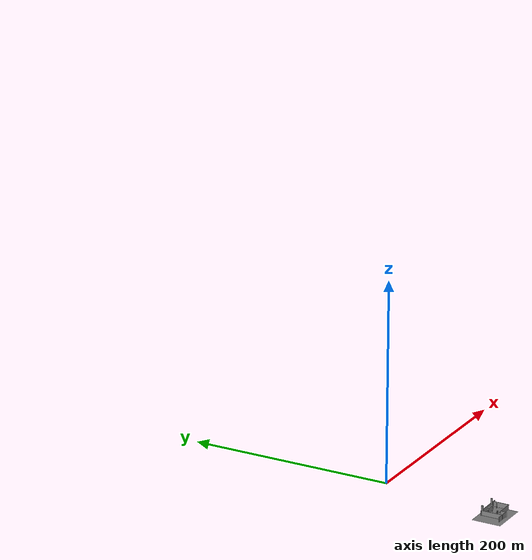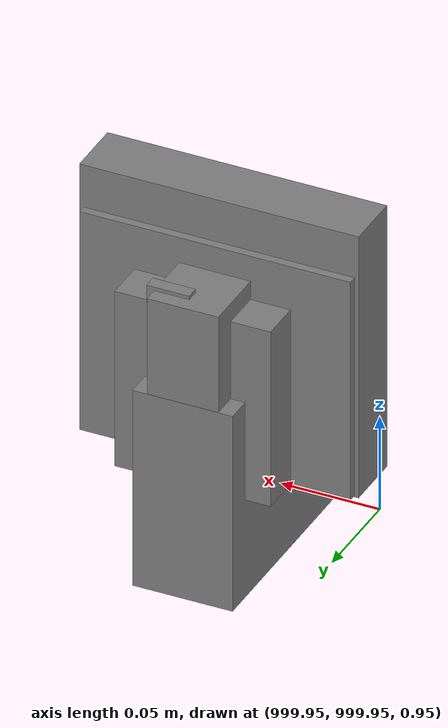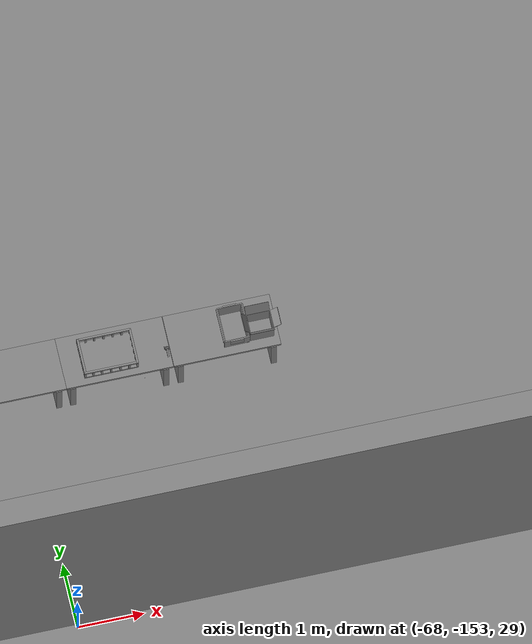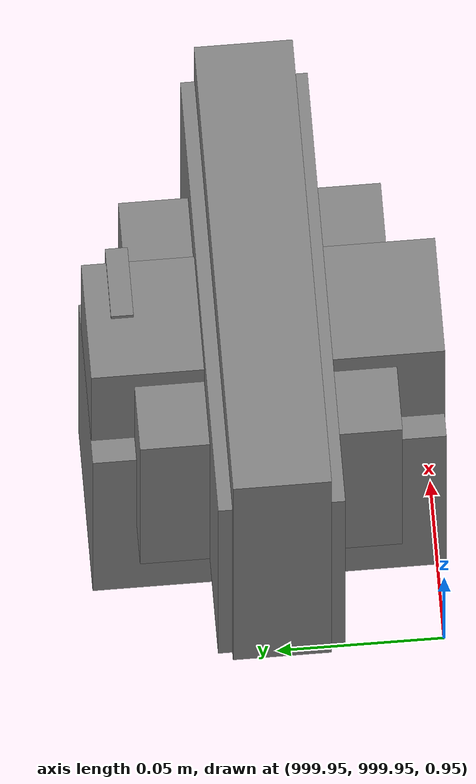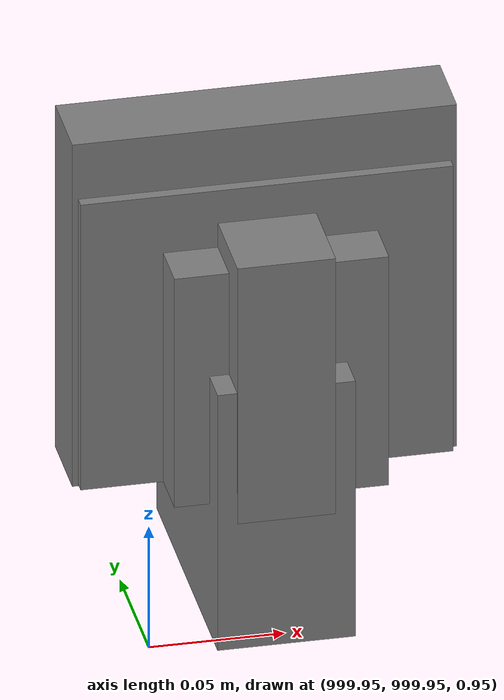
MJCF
<mujoco>
    <option gravity="0.000000000 0.000000000 -9.810000420" timestep="0.0049999999" integrator="implicitfast" density="1.225" viscosity="1.8000001e-05" noslip_iterations="10" iterations="100" sdf_iterations="50">
        <flag multiccd="disable"/>
    </option>
    <size memory="1000M"/>
    <compiler coordinate="local"/>
    <worldbody>
        <light cutoff="30" pos="0 1 1" dir="0 -1 -2"/>
        <light cutoff="30" pos="0 -1 1" dir="0 1 -2"/>
        <body pos="-64.866622925 -149.383972168 30.183746338" euler="89.999984741 89.999946594 0.000000000" name="openloong_gripper_2f85_fix_base_usda_bluebox_01">
            <geom contype="1" conaffinity="1" density="1000" type="box" material="" rgba="0.500000000 0.500000000 0.500000000 1.000000000" solimp="0.899999976 0.949999988 0.001000000" friction="1.000000000 0.005000000 0.000100000" solref="0.020000000 1.000000000" margin="0" condim="3" group="0" pos="0.276580811 0.187225342 0.000068665" quat="0.707106948 0.000077471 0.707106352 0.000077486" size="0.100000001 0.057999998 0.010000000" name="openloong_gripper_2f85_fix_base_usda_geom_E6CB167C_A787_413D_8DF1_69F89B99BAC3"/>
            <geom contype="1" conaffinity="1" density="1000" type="box" material="" rgba="0.500000000 0.500000000 0.500000000 1.000000000" solimp="0.899999976 0.949999988 0.001000000" friction="1.000000000 0.005000000 0.000100000" solref="0.020000000 1.000000000" margin="0" condim="3" group="0" pos="0.000000000 0.002883911 0.000000000" quat="0.999999881 0.000000000 0.000000000 0.000000000" size="0.254000008 0.003000000 0.172000006" name="openloong_gripper_2f85_fix_base_usda_geom_F4586093_CB85_41C2_A930_5C9FCCE098BD"/>
            <geom contype="1" conaffinity="1" density="1000" type="box" material="" rgba="0.500000000 0.500000000 0.500000000 1.000000000" solimp="0.899999976 0.949999988 0.001000000" friction="1.000000000 0.005000000 0.000100000" solref="0.020000000 1.000000000" margin="0" condim="3" group="0" pos="0.000000000 0.124874115 0.173484802" quat="0.999796331 0.020176515 -0.000000015 0.000000030" size="0.259999990 0.119999997 0.007000000" name="openloong_gripper_2f85_fix_base_usda_geom_CA0D871A_0E82_4323_AEB8_789A9F386BD1"/>
            <geom contype="1" conaffinity="1" density="1000" type="box" material="" rgba="0.500000000 0.500000000 0.500000000 1.000000000" solimp="0.899999976 0.949999988 0.001000000" friction="1.000000000 0.005000000 0.000100000" solref="0.020000000 1.000000000" margin="0" condim="3" group="0" pos="0.000000000 0.124874115 -0.173469543" quat="0.999796331 -0.020176545 -0.000000015 0.000000000" size="0.259999990 0.119999997 0.007000000" name="openloong_gripper_2f85_fix_base_usda_geom_D685A71E_26E9_4078_B27A_410F92C00C3D"/>
            <geom contype="1" conaffinity="1" density="1000" type="box" material="" rgba="0.500000000 0.500000000 0.500000000 1.000000000" solimp="0.899999976 0.949999988 0.001000000" friction="1.000000000 0.005000000 0.000100000" solref="0.020000000 1.000000000" margin="0" condim="3" group="0" pos="0.000000000 0.214008331 0.188980103" quat="0.999912977 0.013176724 0.000000015 0.000000000" size="0.259999990 0.029999999 0.012500000" name="openloong_gripper_2f85_fix_base_usda_geom_F272A437_09B5_4889_823D_DC227E046E25"/>
            <geom contype="1" conaffinity="1" density="1000" type="box" material="" rgba="0.500000000 0.500000000 0.500000000 1.000000000" solimp="0.899999976 0.949999988 0.001000000" friction="1.000000000 0.005000000 0.000100000" solref="0.020000000 1.000000000" margin="0" condim="3" group="0" pos="-0.258361816 0.125289917 0.001876831" quat="0.702796936 -0.020792112 0.710783124 0.020769298" size="0.189999998 0.119999997 0.009000000" name="openloong_gripper_2f85_fix_base_usda_geom_7ACE0376_5C8B_4FAF_A59A_97A389C719F7"/>
            <geom contype="1" conaffinity="1" density="1000" type="box" material="" rgba="0.500000000 0.500000000 0.500000000 1.000000000" solimp="0.899999976 0.949999988 0.001000000" friction="1.000000000 0.005000000 0.000100000" solref="0.020000000 1.000000000" margin="0" condim="3" group="0" pos="0.000000000 0.214008331 -0.188980103" quat="0.999912977 -0.013176769 0.000000030 0.000000015" size="0.259999990 0.029999999 0.012500000" name="openloong_gripper_2f85_fix_base_usda_geom_01E7985F_EE26_441E_B8BD_2FA61BE21765"/>
            <geom contype="1" conaffinity="1" density="1000" type="box" material="" rgba="0.500000000 0.500000000 0.500000000 1.000000000" solimp="0.899999976 0.949999988 0.001000000" friction="1.000000000 0.005000000 0.000100000" solref="0.020000000 1.000000000" margin="0" condim="3" group="0" pos="-0.276611328 0.187225342 0.000068665" quat="0.707106650 0.000077441 0.707106709 0.000077456" size="0.100000001 0.057999998 0.010000000" name="openloong_gripper_2f85_fix_base_usda_geom_ED971142_52B0_4D2B_8F00_E6BA2C114097"/>
            <geom contype="1" conaffinity="1" density="1000" type="box" material="" rgba="0.500000000 0.500000000 0.500000000 1.000000000" solimp="0.899999976 0.949999988 0.001000000" friction="1.000000000 0.005000000 0.000100000" solref="0.020000000 1.000000000" margin="0" condim="3" group="0" pos="0.258331299 0.125289917 0.001876831" quat="0.702851415 0.018856421 0.710823774 -0.019329369" size="0.189999998 0.119999997 0.009000000" name="openloong_gripper_2f85_fix_base_usda_geom_4950ABB1_6322_46B4_8864_E85E2EECC0F0"/>
            <freejoint name="openloong_gripper_2f85_fix_base_usda_bluebox_01_joint"/>
            <site size="0.005000000 0.005000000 0.005000000" rgba="0.500000000 0.500000000 0.500000000 1.000000000" pos="0.000000000 0.000000000 0.000000000" quat="0.999961913 0.008726534 0.000000000 0.000000000" group="0" type="sphere" name="openloong_gripper_2f85_fix_base_usda_bluebox_01site"/>
        </body>
        <body pos="-64.496299744 -149.491867065 30.235729218" euler="0.000000000 0.000000000 89.999946594" name="openloong_gripper_2f85_fix_base_usda_cardboardbox_01">
            <geom contype="1" conaffinity="1" density="1000" type="box" material="" rgba="0.500000000 0.500000000 0.500000000 1.000000000" solimp="0.899999976 0.949999988 0.001000000" friction="1.000000000 0.005000000 0.000100000" solref="0.020000000 1.000000000" margin="0" condim="3" group="0" pos="-0.003166199 -0.004086494 0.005052090" quat="1.000000000 0.000000000 0.000000000 0.000000000" size="0.142499998 0.177500010 0.005000000" name="openloong_gripper_2f85_fix_base_usda_geom_3C16E67A_8A08_4244_9FD8_B814B50E6A77"/>
            <geom contype="1" conaffinity="1" density="1000" type="box" material="" rgba="0.500000000 0.500000000 0.500000000 1.000000000" solimp="0.899999976 0.949999988 0.001000000" friction="1.000000000 0.005000000 0.000100000" solref="0.020000000 1.000000000" margin="0" condim="3" group="0" pos="-0.003166199 0.170316696 0.150570869" quat="1.000000000 0.000000000 0.000000000 0.000000000" size="0.142499998 0.005000000 0.149999991" name="openloong_gripper_2f85_fix_base_usda_geom_ADFB0A52_E198_4F53_A20C_8912BF360F4D"/>
            <geom contype="1" conaffinity="1" density="1000" type="box" material="" rgba="0.500000000 0.500000000 0.500000000 1.000000000" solimp="0.899999976 0.949999988 0.001000000" friction="1.000000000 0.005000000 0.000100000" solref="0.020000000 1.000000000" margin="0" condim="3" group="0" pos="-0.147399902 -0.005307198 0.150570869" quat="1.000000000 0.000000000 0.000000000 0.000000000" size="0.005000000 0.177500010 0.149999991" name="openloong_gripper_2f85_fix_base_usda_geom_F8F8CA53_0EF5_40AF_B569_653C6A0A3684"/>
            <geom contype="1" conaffinity="1" density="1000" type="box" material="" rgba="0.500000000 0.500000000 0.500000000 1.000000000" solimp="0.899999976 0.949999988 0.001000000" friction="1.000000000 0.005000000 0.000100000" solref="0.020000000 1.000000000" margin="0" condim="3" group="0" pos="0.140275955 -0.005307198 0.150570869" quat="1.000000000 0.000000000 0.000000000 0.000000000" size="0.005000000 0.177500010 0.149999991" name="openloong_gripper_2f85_fix_base_usda_geom_24BBF9FE_BFF6_4FB1_B4C5_C3E759036A48"/>
            <geom contype="1" conaffinity="1" density="1000" type="box" material="" rgba="0.500000000 0.500000000 0.500000000 1.000000000" solimp="0.899999976 0.949999988 0.001000000" friction="1.000000000 0.005000000 0.000100000" solref="0.020000000 1.000000000" margin="0" condim="3" group="0" pos="-0.003166199 -0.181550980 0.150570869" quat="1.000000000 0.000000000 0.000000000 0.000000000" size="0.142499998 0.005000000 0.149999991" name="openloong_gripper_2f85_fix_base_usda_geom_FA2E4845_D8D4_4244_8ECA_0D16BD961C44"/>
            <freejoint name="openloong_gripper_2f85_fix_base_usda_cardboardbox_01_joint"/>
            <site size="0.005000000 0.005000000 0.005000000" rgba="0.500000000 0.500000000 0.500000000 1.000000000" pos="0.000000000 0.000000000 0.000000000" quat="0.999961913 0.008726535 0.000000000 0.000000000" group="0" type="sphere" name="openloong_gripper_2f85_fix_base_usda_site_3909F4BB_6B42_48F3_890B_DF3222F81FA1"/>
            <body pos="0.139160156 -0.004048347 0.301930904" euler="-179.999954224 49.383502960 179.999954224" name="openloong_gripper_2f85_fix_base_usda_A1_006">
                <geom contype="1" conaffinity="1" density="1000" type="box" material="" rgba="0.500000000 0.500000000 0.500000000 1.000000000" solimp="0.899999976 0.949999988 0.001000000" friction="1.000000000 0.005000000 0.000100000" solref="0.020000000 1.000000000" margin="0" condim="3" group="0" pos="-0.071587563 0.000009537 0.001745224" quat="0.999999881 0.000000000 0.000000000 0.000000000" size="0.071249999 0.179999992 0.002500000" name="openloong_gripper_2f85_fix_base_usda_geom_7DB652F7_7A93_41FF_96B4_E5484C8BD257"/>
                <joint armature="0" stiffness="0.07" damping="0.0099999998" axis="0.000000 1.000000 0.000000" type="hinge" name="openloong_gripper_2f85_fix_base_usda_A1_006"/>
            </body>
            <body pos="-0.145902634 -0.004086494 0.301938057" euler="-180.000000000 -60.000011444 -180.000000000" name="openloong_gripper_2f85_fix_base_usda_A2_006">
                <geom contype="1" conaffinity="1" density="1000" type="box" material="" rgba="0.500000000 0.500000000 0.500000000 1.000000000" solimp="0.899999976 0.949999988 0.001000000" friction="1.000000000 0.005000000 0.000100000" solref="0.020000000 1.000000000" margin="0" condim="3" group="0" pos="0.071268082 0.000009537 0.002717972" quat="0.000002921 0.000000000 -0.000000030 0.999999881" size="0.071249999 0.179999992 0.002500000" name="openloong_gripper_2f85_fix_base_usda_geom_3C373177_E74D_4DDC_9873_3F9739E55136"/>
                <joint armature="0" stiffness="0.07" damping="0.0099999998" axis="0.000000 1.000000 0.000000" type="hinge" name="openloong_gripper_2f85_fix_base_usda_A2_006"/>
            </body>
            <body pos="-0.003385544 0.175991058 0.301930904" euler="-125.858116150 -0.000004561 0.000002331" name="openloong_gripper_2f85_fix_base_usda_B2_006">
                <geom contype="1" conaffinity="1" density="1000" type="box" material="" rgba="0.500000000 0.500000000 0.500000000 1.000000000" solimp="0.899999976 0.949999988 0.001000000" friction="1.000000000 0.005000000 0.000100000" solref="0.020000000 1.000000000" margin="0" condim="3" group="0" pos="0.000009537 -0.070939064 -0.002470016" quat="0.999614120 0.027776197 -0.000000015 0.000000030" size="0.137500003 0.064999998 0.005000000" name="openloong_gripper_2f85_fix_base_usda_geom_AE7393DD_8B21_4BB7_AADA_896BE0B39BB9"/>
                <joint armature="0" stiffness="0.07" damping="0.0099999998" axis="1.000000 0.000000 0.000000" type="hinge" name="openloong_gripper_2f85_fix_base_usda_B2_006"/>
            </body>
            <body pos="-0.003385544 -0.184140205 0.301938057" euler="147.805557251 0.000000000 0.000000000" name="openloong_gripper_2f85_fix_base_usda_B1_006">
                <geom contype="1" conaffinity="1" density="1000" type="box" material="" rgba="0.500000000 0.500000000 0.500000000 1.000000000" solimp="0.899999976 0.949999988 0.001000000" friction="1.000000000 0.005000000 0.000100000" solref="0.020000000 1.000000000" margin="0" condim="3" group="0" pos="-0.000028610 0.070202351 -0.002703667" quat="0.999614179 -0.027776167 0.000000000 0.000000000" size="0.137500003 0.064999998 0.005000000" name="openloong_gripper_2f85_fix_base_usda_geom_E5D0FAB4_6C62_4AA7_BBCB_A4D082F695B8"/>
                <joint armature="0" stiffness="0.07" damping="0.0099999998" axis="1.000000 0.000000 0.000000" type="hinge" name="openloong_gripper_2f85_fix_base_usda_B1_006"/>
            </body>
        </body>
        <body pos="-65.882858276 -149.481979370 30.229999542" euler="-64.487716675 0.000000000 0.000000000" name="openloong_gripper_2f85_fix_base_usda_Barcode">
            <geom contype="1" conaffinity="1" density="1000" type="box" material="" rgba="0.500000000 0.500000000 0.500000000 1.000000000" solimp="0.899999976 0.949999988 0.001000000" friction="1.000000000 0.005000000 0.000100000" solref="0.020000000 1.000000000" margin="0" condim="3" group="0" pos="0.000000000 0.013038635 0.001419067" quat="0.000000000 0.000000000 0.000000000 1.000000119" size="0.034000002 0.010000000 0.017999999" name="openloong_gripper_2f85_fix_base_usda_geom_4ED190F7_07AE_4E4B_AF08_BE568BEE8BF3"/>
            <geom contype="1" conaffinity="1" density="1000" type="box" material="" rgba="0.500000000 0.500000000 0.500000000 1.000000000" solimp="0.899999976 0.949999988 0.001000000" friction="1.000000000 0.005000000 0.000100000" solref="0.020000000 1.000000000" margin="0" condim="3" group="0" pos="0.000000000 -0.035301208 -0.007095337" quat="0.000000000 0.000000000 -0.043619365 0.999048233" size="0.028999999 0.010000000 0.020000000" name="openloong_gripper_2f85_fix_base_usda_geom_0AF573D8_270F_4796_8C9A_4C0B090C6E79"/>
            <geom contype="1" conaffinity="1" density="1000" type="box" material="" rgba="0.500000000 0.500000000 0.500000000 1.000000000" solimp="0.899999976 0.949999988 0.001000000" friction="1.000000000 0.005000000 0.000100000" solref="0.020000000 1.000000000" margin="0" condim="3" group="0" pos="0.000000000 -0.043411255 -0.011749268" quat="0.922262907 0.386563420 0.000000000 0.000000000" size="0.026000001 0.010000000 0.020000000" name="openloong_gripper_2f85_fix_base_usda_geom_A97E3A9E_6754_4E9A_A2E0_ED5CE798A1A8"/>
            <geom contype="1" conaffinity="1" density="1000" type="box" material="" rgba="0.500000000 0.500000000 0.500000000 1.000000000" solimp="0.899999976 0.949999988 0.001000000" friction="1.000000000 0.005000000 0.000100000" solref="0.020000000 1.000000000" margin="0" condim="3" group="0" pos="0.000000000 -0.016967773 -0.031860352" quat="0.000000000 0.000000000 0.000000000 1.000000119" size="0.008000000 0.010000000 0.013000000" name="openloong_gripper_2f85_fix_base_usda_geom_4D05A425_6A8F_4644_A05D_01C806CF50DF"/>
            <geom contype="1" conaffinity="1" density="1000" type="box" material="" rgba="0.500000000 0.500000000 0.500000000 1.000000000" solimp="0.899999976 0.949999988 0.001000000" friction="1.000000000 0.005000000 0.000100000" solref="0.020000000 1.000000000" margin="0" condim="3" group="0" pos="0.000000000 -0.001869202 0.000312805" quat="0.953716993 0.300705761 0.000000000 0.000000000" size="0.032000002 0.010000000 0.018999999" name="openloong_gripper_2f85_fix_base_usda_geom_DCEFCA60_77DF_4194_AAAB_9BD5D5A99067"/>
            <geom contype="1" conaffinity="1" density="1000" type="box" material="" rgba="0.500000000 0.500000000 0.500000000 1.000000000" solimp="0.899999976 0.949999988 0.001000000" friction="1.000000000 0.005000000 0.000100000" solref="0.020000000 1.000000000" margin="0" condim="3" group="0" pos="0.000000000 -0.019531250 -0.003173828" quat="0.953716993 0.300705761 0.000000000 0.000000000" size="0.030999999 0.010000000 0.020000000" name="openloong_gripper_2f85_fix_base_usda_geom_DDFA3985_A9FA_4A37_B213_7BF6BF2A25C2"/>
            <geom contype="1" conaffinity="1" density="1000" type="box" material="" rgba="0.500000000 0.500000000 0.500000000 1.000000000" solimp="0.899999976 0.949999988 0.001000000" friction="1.000000000 0.005000000 0.000100000" solref="0.020000000 1.000000000" margin="0" condim="3" group="0" pos="0.000000000 -0.035301208 -0.007095337" quat="0.953716993 0.300705761 0.000000000 0.000000000" size="0.028999999 0.010000000 0.020000000" name="openloong_gripper_2f85_fix_base_usda_geom_AC86F25D_6233_4751_A525_2D6D98C029F6"/>
            <geom contype="1" conaffinity="1" density="1000" type="box" material="" rgba="0.500000000 0.500000000 0.500000000 1.000000000" solimp="0.899999976 0.949999988 0.001000000" friction="1.000000000 0.005000000 0.000100000" solref="0.020000000 1.000000000" margin="0" condim="3" group="0" pos="0.000000000 -0.042617798 -0.071121216" quat="0.000000000 0.000000000 0.000000000 1.000000119" size="0.013000000 0.021000000 0.059999999" name="openloong_gripper_2f85_fix_base_usda_geom_1C631054_259E_4E18_BBEA_0044749E2BD8"/>
            <freejoint name="openloong_gripper_2f85_fix_base_usda_Barcode_joint"/>
            <site size="0.005000000 0.005000000 0.005000000" rgba="0.500000000 0.500000000 0.500000000 1.000000000" pos="0.000000000 0.000000000 0.000000000" quat="1.000000000 0.000000000 0.000000000 0.000000000" group="0" type="sphere" name="openloong_gripper_2f85_fix_base_usda_Barcode_site"/>
        </body>
        <body pos="-66.745018005 -149.392349243 30.184000015" euler="0.000000000 0.000000000 89.999946594" name="[22330593104827]_Basket_01">
            <geom contype="1" conaffinity="1" density="1000" type="box" material="" rgba="0.500000000 0.500000000 0.500000000 1.000000000" solimp="0.899999976 0.949999988 0.001000000" friction="1.000000000 0.005000000 0.000100000" solref="0.020000000 1.000000000" margin="0" condim="3" group="0" pos="-0.052425385 0.389207840 0.089787483" quat="0.707107008 0.000000000 0.000000000 0.707106411" size="0.014249999 0.014249999 0.059999999" name="[22330593104827]_geom_5438B2E9_1B79_4F96_A7EF_2D5E11674B4C"/>
            <geom contype="1" conaffinity="1" density="1000" type="box" material="" rgba="0.500000000 0.500000000 0.500000000 1.000000000" solimp="0.899999976 0.949999988 0.001000000" friction="1.000000000 0.005000000 0.000100000" solref="0.020000000 1.000000000" margin="0" condim="3" group="0" pos="0.264015198 -0.133043289 0.089787483" quat="0.707107008 0.000000000 0.000000000 0.707106411" size="0.014249999 0.014249999 0.059999999" name="[22330593104827]_geom_FEBCAEFA_5A52_4CFE_89C2_AB99B9099F1C"/>
            <geom contype="1" conaffinity="1" density="1000" type="box" material="" rgba="0.500000000 0.500000000 0.500000000 1.000000000" solimp="0.899999976 0.949999988 0.001000000" friction="1.000000000 0.005000000 0.000100000" solref="0.020000000 1.000000000" margin="0" condim="3" group="0" pos="-0.264015198 -0.265548706 0.089793205" quat="0.707107008 0.000000000 0.000000000 0.707106411" size="0.014249999 0.014249999 0.059999999" name="[22330593104827]_geom_F41F966F_245B_41B9_9086_639A1D47DE28"/>
            <geom contype="1" conaffinity="1" density="1000" type="box" material="" rgba="0.500000000 0.500000000 0.500000000 1.000000000" solimp="0.899999976 0.949999988 0.001000000" friction="1.000000000 0.005000000 0.000100000" solref="0.020000000 1.000000000" margin="0" condim="3" group="0" pos="-0.160263062 -0.389322281 0.089793205" quat="0.707107008 0.000000000 0.000000000 0.707106411" size="0.014249999 0.014249999 0.059999999" name="[22330593104827]_geom_A6A3F5B9_B64E_47E5_A2EC_CC68EC2BDE23"/>
            <geom contype="1" conaffinity="1" density="1000" type="box" material="" rgba="0.500000000 0.500000000 0.500000000 1.000000000" solimp="0.899999976 0.949999988 0.001000000" friction="1.000000000 0.005000000 0.000100000" solref="0.020000000 1.000000000" margin="0" condim="3" group="0" pos="0.162265778 -0.389322281 0.089787483" quat="0.707107008 0.000000000 0.000000000 0.707106411" size="0.014249999 0.014249999 0.059999999" name="[22330593104827]_geom_D67CC536_900A_4D52_BDEE_FB02DDC6E8DD"/>
            <geom contype="1" conaffinity="1" density="1000" type="box" material="" rgba="0.500000000 0.500000000 0.500000000 1.000000000" solimp="0.899999976 0.949999988 0.001000000" friction="1.000000000 0.005000000 0.000100000" solref="0.020000000 1.000000000" margin="0" condim="3" group="0" pos="0.264015198 0.389207840 0.089787483" quat="0.707107008 0.000000000 0.000000000 0.707106411" size="0.014249999 0.014249999 0.059999999" name="[22330593104827]_geom_F6FBC78D_1C17_4938_A5CB_1BC33AFB471D"/>
            <geom contype="1" conaffinity="1" density="1000" type="box" material="" rgba="0.500000000 0.500000000 0.500000000 1.000000000" solimp="0.899999976 0.949999988 0.001000000" friction="1.000000000 0.005000000 0.000100000" solref="0.020000000 1.000000000" margin="0" condim="3" group="0" pos="-0.264015198 -0.133043289 0.089793205" quat="0.707107008 0.000000000 0.000000000 0.707106411" size="0.014249999 0.014249999 0.059999999" name="[22330593104827]_geom_ABDC82AA_BC22_4149_B1E0_D68F958EA2C2"/>
            <geom contype="1" conaffinity="1" density="1000" type="box" material="" rgba="0.500000000 0.500000000 0.500000000 1.000000000" solimp="0.899999976 0.949999988 0.001000000" friction="1.000000000 0.005000000 0.000100000" solref="0.020000000 1.000000000" margin="0" condim="3" group="0" pos="-0.264026642 0.269256592 0.089793205" quat="0.707107008 0.000000000 0.000000000 0.707106411" size="0.014249999 0.014249999 0.059999999" name="[22330593104827]_geom_282D4F7D_1D90_44B0_B326_13B51484C06E"/>
            <geom contype="1" conaffinity="1" density="1000" type="box" material="" rgba="0.500000000 0.500000000 0.500000000 1.000000000" solimp="0.899999976 0.949999988 0.001000000" friction="1.000000000 0.005000000 0.000100000" solref="0.020000000 1.000000000" margin="0" condim="3" group="0" pos="0.054462433 0.389207840 0.089787483" quat="0.707107008 0.000000000 0.000000000 0.707106411" size="0.014249999 0.014249999 0.059999999" name="[22330593104827]_geom_6F681C73_B81A_4DF7_A51C_C65F6E483A02"/>
            <geom contype="1" conaffinity="1" density="1000" type="box" material="" rgba="0.500000000 0.500000000 0.500000000 1.000000000" solimp="0.899999976 0.949999988 0.001000000" friction="1.000000000 0.005000000 0.000100000" solref="0.020000000 1.000000000" margin="0" condim="3" group="0" pos="0.054462433 -0.389322281 0.089787483" quat="0.707107008 0.000000000 0.000000000 0.707106411" size="0.014249999 0.014249999 0.059999999" name="[22330593104827]_geom_E6C04B10_B987_4C9D_9F54_D2AA324C9B75"/>
            <geom contype="1" conaffinity="1" density="1000" type="box" material="" rgba="0.500000000 0.500000000 0.500000000 1.000000000" solimp="0.899999976 0.949999988 0.001000000" friction="1.000000000 0.005000000 0.000100000" solref="0.020000000 1.000000000" margin="0" condim="3" group="0" pos="0.264015198 0.269256592 0.089793205" quat="0.707107008 0.000000000 0.000000000 0.707106411" size="0.014249999 0.014249999 0.059999999" name="[22330593104827]_geom_13793825_5A0E_455C_818A_86C01ADD9505"/>
            <geom contype="1" conaffinity="1" density="1000" type="box" material="" rgba="0.500000000 0.500000000 0.500000000 1.000000000" solimp="0.899999976 0.949999988 0.001000000" friction="1.000000000 0.005000000 0.000100000" solref="0.020000000 1.000000000" margin="0" condim="3" group="0" pos="0.264015198 -0.389322281 0.089787483" quat="0.707107008 0.000000000 0.000000000 0.707106411" size="0.014249999 0.014249999 0.059999999" name="[22330593104827]_geom_F5F0681E_B9BD_42B4_A446_4018523EFCEE"/>
            <geom contype="1" conaffinity="1" density="1000" type="box" material="" rgba="0.500000000 0.500000000 0.500000000 1.000000000" solimp="0.899999976 0.949999988 0.001000000" friction="1.000000000 0.005000000 0.000100000" solref="0.020000000 1.000000000" margin="0" condim="3" group="0" pos="0.000000000 0.000000000 0.015998840" quat="0.707107008 0.000000000 0.000000000 0.707106411" size="0.403499991 0.279000014 0.015750000" name="[22330593104827]_geom_CE17DE8D_DBC9_42E7_88ED_1974A2893195"/>
            <geom contype="1" conaffinity="1" density="1000" type="box" material="" rgba="0.500000000 0.500000000 0.500000000 1.000000000" solimp="0.899999976 0.949999988 0.001000000" friction="1.000000000 0.005000000 0.000100000" solref="0.020000000 1.000000000" margin="0" condim="3" group="0" pos="0.000000000 -0.389476776 0.163619041" quat="0.707107008 0.000000000 0.000000000 0.707106411" size="0.015000000 0.277500004 0.015750000" name="[22330593104827]_geom_E7E62287_8385_40E9_BAE8_387012D52708"/>
            <geom contype="1" conaffinity="1" density="1000" type="box" material="" rgba="0.500000000 0.500000000 0.500000000 1.000000000" solimp="0.899999976 0.949999988 0.001000000" friction="1.000000000 0.005000000 0.000100000" solref="0.020000000 1.000000000" margin="0" condim="3" group="0" pos="0.162265778 0.389207840 0.089787483" quat="0.707107008 0.000000000 0.000000000 0.707106411" size="0.014249999 0.014249999 0.059999999" name="[22330593104827]_geom_1843ACAB_D320_447A_97D0_257B2D0A56A4"/>
            <geom contype="1" conaffinity="1" density="1000" type="box" material="" rgba="0.500000000 0.500000000 0.500000000 1.000000000" solimp="0.899999976 0.949999988 0.001000000" friction="1.000000000 0.005000000 0.000100000" solref="0.020000000 1.000000000" margin="0" condim="3" group="0" pos="0.000000000 0.389471054 0.163619041" quat="0.707107008 0.000000000 0.000000000 0.707106411" size="0.015000000 0.277500004 0.015750000" name="[22330593104827]_geom_0162D3E4_9210_4716_8095_8E17E7F8C514"/>
            <geom contype="1" conaffinity="1" density="1000" type="box" material="" rgba="0.500000000 0.500000000 0.500000000 1.000000000" solimp="0.899999976 0.949999988 0.001000000" friction="1.000000000 0.005000000 0.000100000" solref="0.020000000 1.000000000" margin="0" condim="3" group="0" pos="-0.263511658 0.000000000 0.163619041" quat="0.707107008 0.000000000 0.000000000 0.707106411" size="0.403499991 0.015000000 0.015750000" name="[22330593104827]_geom_7A1019A5_2A86_44C6_BE12_24E515135489"/>
            <geom contype="1" conaffinity="1" density="1000" type="box" material="" rgba="0.500000000 0.500000000 0.500000000 1.000000000" solimp="0.899999976 0.949999988 0.001000000" friction="1.000000000 0.005000000 0.000100000" solref="0.020000000 1.000000000" margin="0" condim="3" group="0" pos="-0.264015198 0.141334534 0.089793205" quat="0.707107008 0.000000000 0.000000000 0.707106411" size="0.014249999 0.014249999 0.059999999" name="[22330593104827]_geom_84ABFCF8_4029_4ADA_9D5D_C3A5B2CC3760"/>
            <geom contype="1" conaffinity="1" density="1000" type="box" material="" rgba="0.500000000 0.500000000 0.500000000 1.000000000" solimp="0.899999976 0.949999988 0.001000000" friction="1.000000000 0.005000000 0.000100000" solref="0.020000000 1.000000000" margin="0" condim="3" group="0" pos="0.264015198 -0.265548706 0.089787483" quat="0.707107008 0.000000000 0.000000000 0.707106411" size="0.014249999 0.014249999 0.059999999" name="[22330593104827]_geom_9DB7A771_FAA7_468B_8968_C1A4D39D30A1"/>
            <geom contype="1" conaffinity="1" density="1000" type="box" material="" rgba="0.500000000 0.500000000 0.500000000 1.000000000" solimp="0.899999976 0.949999988 0.001000000" friction="1.000000000 0.005000000 0.000100000" solref="0.020000000 1.000000000" margin="0" condim="3" group="0" pos="-0.160263062 0.389207840 0.089787483" quat="0.707107008 0.000000000 0.000000000 0.707106411" size="0.014249999 0.014249999 0.059999999" name="[22330593104827]_geom_100FEEE7_1322_4198_B8C9_8DB6FD844EBA"/>
            <geom contype="1" conaffinity="1" density="1000" type="box" material="" rgba="0.500000000 0.500000000 0.500000000 1.000000000" solimp="0.899999976 0.949999988 0.001000000" friction="1.000000000 0.005000000 0.000100000" solref="0.020000000 1.000000000" margin="0" condim="3" group="0" pos="-0.052425385 -0.389322281 0.089787483" quat="0.707107008 0.000000000 0.000000000 0.707106411" size="0.014249999 0.014249999 0.059999999" name="[22330593104827]_geom_3A60B78B_E1EA_4FD5_AC66_1EF3B961DF91"/>
            <geom contype="1" conaffinity="1" density="1000" type="box" material="" rgba="0.500000000 0.500000000 0.500000000 1.000000000" solimp="0.899999976 0.949999988 0.001000000" friction="1.000000000 0.005000000 0.000100000" solref="0.020000000 1.000000000" margin="0" condim="3" group="0" pos="-0.264026642 -0.389322281 0.089793205" quat="0.707107008 0.000000000 0.000000000 0.707106411" size="0.014249999 0.014249999 0.059999999" name="[22330593104827]_geom_E3AC0B43_8C33_4A28_A53A_B36A904A5A8C"/>
            <geom contype="1" conaffinity="1" density="1000" type="box" material="" rgba="0.500000000 0.500000000 0.500000000 1.000000000" solimp="0.899999976 0.949999988 0.001000000" friction="1.000000000 0.005000000 0.000100000" solref="0.020000000 1.000000000" margin="0" condim="3" group="0" pos="0.264015198 0.141334534 0.089787483" quat="0.707107008 0.000000000 0.000000000 0.707106411" size="0.014249999 0.014249999 0.059999999" name="[22330593104827]_geom_1A48537B_30FA_46E8_8A3D_3924DF84C2B9"/>
            <geom contype="1" conaffinity="1" density="1000" type="box" material="" rgba="0.500000000 0.500000000 0.500000000 1.000000000" solimp="0.899999976 0.949999988 0.001000000" friction="1.000000000 0.005000000 0.000100000" solref="0.020000000 1.000000000" margin="0" condim="3" group="0" pos="-0.264015198 0.389207840 0.089793205" quat="0.707107008 0.000000000 0.000000000 0.707106411" size="0.014249999 0.014249999 0.059999999" name="[22330593104827]_geom_7B088FCB_21A3_4830_8233_EEB2BA3CBC3A"/>
            <geom contype="1" conaffinity="1" density="1000" type="box" material="" rgba="0.500000000 0.500000000 0.500000000 1.000000000" solimp="0.899999976 0.949999988 0.001000000" friction="1.000000000 0.005000000 0.000100000" solref="0.020000000 1.000000000" margin="0" condim="3" group="0" pos="0.264015198 0.004480362 0.089787483" quat="0.707107008 0.000000000 0.000000000 0.707106411" size="0.014249999 0.014249999 0.059999999" name="[22330593104827]_geom_DA8C6FFF_E400_4188_800A_DF7A7A718B71"/>
            <geom contype="1" conaffinity="1" density="1000" type="box" material="" rgba="0.500000000 0.500000000 0.500000000 1.000000000" solimp="0.899999976 0.949999988 0.001000000" friction="1.000000000 0.005000000 0.000100000" solref="0.020000000 1.000000000" margin="0" condim="3" group="0" pos="0.263694763 -0.000011444 0.163619041" quat="0.707107008 0.000000000 0.000000000 0.707106411" size="0.403499991 0.015000000 0.015750000" name="[22330593104827]_geom_8BD55D60_3140_4477_B69D_410FAEE324CF"/>
            <geom contype="1" conaffinity="1" density="1000" type="box" material="" rgba="0.500000000 0.500000000 0.500000000 1.000000000" solimp="0.899999976 0.949999988 0.001000000" friction="1.000000000 0.005000000 0.000100000" solref="0.020000000 1.000000000" margin="0" condim="3" group="0" pos="-0.264015198 0.004480362 0.089793205" quat="0.707107008 0.000000000 0.000000000 0.707106411" size="0.014249999 0.014249999 0.059999999" name="[22330593104827]_geom_D7A431FC_F898_4126_BD5B_63DDB62604D1"/>
            <freejoint name="[22330593104827]_joint_9CB36424_3257_46C5_BF0E_51E81E7301A8"/>
        </body>
        <body pos="0.000000000 0.000000000 0.000000000" euler="0.000000000 0.000000000 0.000000000" name="Static Objects_Static Objects">
            <geom contype="1" conaffinity="1" density="1000" type="box" material="" rgba="0.500000000 0.500000000 0.500000000 1.000000000" solimp="0.899999976 0.949999988 0.001000000" friction="1.000000000 0.005000000 0.000100000" solref="0.020000000 1.000000000" margin="0" condim="3" group="0" pos="-67.544113159 -149.365814209 29.727830887" quat="0.500000417 0.499999970 0.499999553 0.499999970" size="0.381000012 0.319999993 0.041000001" name="Static Objects_geom_D8E44D0A_5504_4CE5_90AD_777F195C9737"/>
            <geom contype="1" conaffinity="1" density="1000" type="box" material="" rgba="0.500000000 0.500000000 0.500000000 1.000000000" solimp="0.899999976 0.949999988 0.001000000" friction="1.000000000 0.005000000 0.000100000" solref="0.020000000 1.000000000" margin="0" condim="3" group="0" pos="-68.239501953 -149.365814209 30.086868286" quat="0.500000417 0.499999970 0.499999553 0.499999970" size="0.370999992 0.039500002 0.745000005" name="Static Objects_geom_5FB99EC9_2703_40F2_85EE_C2930DA6F071"/>
            <geom contype="1" conaffinity="1" density="1000" type="box" material="" rgba="0.500000000 0.500000000 0.500000000 1.000000000" solimp="0.899999976 0.949999988 0.001000000" friction="1.000000000 0.005000000 0.000100000" solref="0.020000000 1.000000000" margin="0" condim="3" group="0" pos="-68.239501953 -149.365814209 30.147235870" quat="0.500000417 0.499999970 0.499999553 0.499999970" size="0.400000006 0.022000000 0.800000012" name="Static Objects_geom_6D19E7DA_420C_42F5_96CB_78E947182D4D"/>
            <geom contype="1" conaffinity="1" density="1000" type="box" material="" rgba="0.500000000 0.500000000 0.500000000 1.000000000" solimp="0.899999976 0.949999988 0.001000000" friction="1.000000000 0.005000000 0.000100000" solref="0.020000000 1.000000000" margin="0" condim="3" group="0" pos="-68.934890747 -149.365814209 29.727830887" quat="0.500000417 0.499999970 0.499999553 0.499999970" size="0.381000012 0.319999993 0.041000001" name="Static Objects_geom_490625CB_7F57_4AB1_8995_A8361AC48932"/>
            <geom contype="1" conaffinity="1" density="1000" type="box" material="" rgba="0.500000000 0.500000000 0.500000000 1.000000000" solimp="0.899999976 0.949999988 0.001000000" friction="1.000000000 0.005000000 0.000100000" solref="0.020000000 1.000000000" margin="0" condim="3" group="0" pos="-68.239501953 -149.365814209 29.561563492" quat="0.500000417 0.499999970 0.499999553 0.499999970" size="0.020000000 0.022000000 0.660000026" name="Static Objects_geom_EBC9C9E4_AE52_42B7_A8B9_5B59F0F0E340"/>
            <geom contype="1" conaffinity="1" density="1000" type="box" material="" rgba="0.500000000 0.500000000 0.500000000 1.000000000" solimp="0.899999976 0.949999988 0.001000000" friction="1.000000000 0.005000000 0.000100000" solref="0.020000000 1.000000000" margin="0" condim="3" group="0" pos="-65.945671082 -149.365814209 29.727830887" quat="0.500000417 0.499999970 0.499999553 0.499999970" size="0.381000012 0.319999993 0.041000001" name="Static Objects_geom_66536A39_81FF_4CC8_914D_3339C037D529"/>
            <geom contype="1" conaffinity="1" density="1000" type="box" material="" rgba="0.500000000 0.500000000 0.500000000 1.000000000" solimp="0.899999976 0.949999988 0.001000000" friction="1.000000000 0.005000000 0.000100000" solref="0.020000000 1.000000000" margin="0" condim="3" group="0" pos="-66.641059875 -149.365814209 30.086868286" quat="0.500000417 0.499999970 0.499999553 0.499999970" size="0.370999992 0.039500002 0.745000005" name="Static Objects_geom_8E059E52_A280_4FC8_BD2B_EB665D4AB755"/>
            <geom contype="1" conaffinity="1" density="1000" type="box" material="" rgba="0.500000000 0.500000000 0.500000000 1.000000000" solimp="0.899999976 0.949999988 0.001000000" friction="1.000000000 0.005000000 0.000100000" solref="0.020000000 1.000000000" margin="0" condim="3" group="0" pos="-66.641059875 -149.365814209 30.147235870" quat="0.500000417 0.499999970 0.499999553 0.499999970" size="0.400000006 0.022000000 0.800000012" name="Static Objects_geom_EAE77ADA_DA9C_4419_9B08_E1D2B5FF1939"/>
            <geom contype="1" conaffinity="1" density="1000" type="box" material="" rgba="0.500000000 0.500000000 0.500000000 1.000000000" solimp="0.899999976 0.949999988 0.001000000" friction="1.000000000 0.005000000 0.000100000" solref="0.020000000 1.000000000" margin="0" condim="3" group="0" pos="-67.336448669 -149.365814209 29.727830887" quat="0.500000417 0.499999970 0.499999553 0.499999970" size="0.381000012 0.319999993 0.041000001" name="Static Objects_geom_470C37C7_0501_475F_8368_1BB404A90C76"/>
            <geom contype="1" conaffinity="1" density="1000" type="box" material="" rgba="0.500000000 0.500000000 0.500000000 1.000000000" solimp="0.899999976 0.949999988 0.001000000" friction="1.000000000 0.005000000 0.000100000" solref="0.020000000 1.000000000" margin="0" condim="3" group="0" pos="-66.641059875 -149.365814209 29.561563492" quat="0.500000417 0.499999970 0.499999553 0.499999970" size="0.020000000 0.022000000 0.660000026" name="Static Objects_geom_30D322E4_D10E_4A8C_8753_369636F8401F"/>
            <geom contype="1" conaffinity="1" density="1000" type="box" material="" rgba="0.500000000 0.500000000 0.500000000 1.000000000" solimp="0.899999976 0.949999988 0.001000000" friction="1.000000000 0.005000000 0.000100000" solref="0.020000000 1.000000000" margin="0" condim="3" group="0" pos="-64.338577271 -149.365814209 29.727830887" quat="0.500000417 0.499999970 0.499999553 0.499999970" size="0.381000012 0.319999993 0.041000001" name="Static Objects_geom_078BB2F0_3EAE_446F_B018_52BCB9D27D48"/>
            <geom contype="1" conaffinity="1" density="1000" type="box" material="" rgba="0.500000000 0.500000000 0.500000000 1.000000000" solimp="0.899999976 0.949999988 0.001000000" friction="1.000000000 0.005000000 0.000100000" solref="0.020000000 1.000000000" margin="0" condim="3" group="0" pos="-65.033966064 -149.365814209 30.086868286" quat="0.500000417 0.499999970 0.499999553 0.499999970" size="0.370999992 0.039500002 0.745000005" name="Static Objects_geom_06CE8EAE_791C_43AC_A8E0_D260E8EDE876"/>
            <geom contype="1" conaffinity="1" density="1000" type="box" material="" rgba="0.500000000 0.500000000 0.500000000 1.000000000" solimp="0.899999976 0.949999988 0.001000000" friction="1.000000000 0.005000000 0.000100000" solref="0.020000000 1.000000000" margin="0" condim="3" group="0" pos="-65.033966064 -149.365814209 30.147235870" quat="0.500000417 0.499999970 0.499999553 0.499999970" size="0.400000006 0.022000000 0.800000012" name="Static Objects_geom_B1D47686_4473_4691_9AA7_EE990F5DD027"/>
            <geom contype="1" conaffinity="1" density="1000" type="box" material="" rgba="0.500000000 0.500000000 0.500000000 1.000000000" solimp="0.899999976 0.949999988 0.001000000" friction="1.000000000 0.005000000 0.000100000" solref="0.020000000 1.000000000" margin="0" condim="3" group="0" pos="-65.729354858 -149.365814209 29.727830887" quat="0.500000417 0.499999970 0.499999553 0.499999970" size="0.381000012 0.319999993 0.041000001" name="Static Objects_geom_5268E133_430C_42A1_AF17_2A8A604B67B0"/>
            <geom contype="1" conaffinity="1" density="1000" type="box" material="" rgba="0.500000000 0.500000000 0.500000000 1.000000000" solimp="0.899999976 0.949999988 0.001000000" friction="1.000000000 0.005000000 0.000100000" solref="0.020000000 1.000000000" margin="0" condim="3" group="0" pos="-65.033966064 -149.365814209 29.561563492" quat="0.500000417 0.499999970 0.499999553 0.499999970" size="0.020000000 0.022000000 0.660000026" name="Static Objects_geom_EBEDF21C_E051_4A4A_9194_7787778D537F"/>
            <geom contype="1" conaffinity="1" density="1000" type="box" material="" rgba="0.500000000 0.500000000 0.500000000 1.000000000" solimp="0.899999976 0.949999988 0.001000000" friction="1.000000000 0.005000000 0.000100000" solref="0.020000000 1.000000000" margin="0" condim="3" group="0" pos="-61.754566193 -137.853729248 33.906845093" quat="0.707107067 0.000000000 0.000000000 0.707106471" size="0.759999990 0.759999990 4.500000000" name="Static Objects_geom_8EDF97DC_E4E6_4606_85E2_10924988C759"/>
            <geom contype="1" conaffinity="1" density="1000" type="box" material="" rgba="0.500000000 0.500000000 0.500000000 1.000000000" solimp="0.899999976 0.949999988 0.001000000" friction="1.000000000 0.005000000 0.000100000" solref="0.020000000 1.000000000" margin="0" condim="3" group="0" pos="-57.511135101 -144.927108765 31.707921982" quat="1.000000000 0.000000000 0.000000000 0.000000000" size="0.200000003 8.000000000 2.299999952" name="Static Objects_geom_8DBAA511_7360_4975_A2DA_ECB4452EA540"/>
            <geom contype="1" conaffinity="1" density="1000" type="box" material="" rgba="0.500000000 0.500000000 0.500000000 1.000000000" solimp="0.899999976 0.949999988 0.001000000" friction="1.000000000 0.005000000 0.000100000" solref="0.020000000 1.000000000" margin="0" condim="3" group="0" pos="-80.517646790 -157.574050903 31.688196182" quat="0.707107067 0.000000000 0.000000000 0.707106471" size="0.600000024 0.600000024 2.299999952" name="Static Objects_geom_9BC6D78A_3BDB_4605_91BB_0D41D8140BDF"/>
            <geom contype="1" conaffinity="1" density="1000" type="box" material="" rgba="0.500000000 0.500000000 0.500000000 1.000000000" solimp="0.899999976 0.949999988 0.001000000" friction="1.000000000 0.005000000 0.000100000" solref="0.020000000 1.000000000" margin="0" condim="3" group="0" pos="-80.711044312 -147.414932251 31.666158676" quat="1.000000000 0.000000000 0.000000000 0.000000000" size="0.200000003 10.000000000 2.299999952" name="Static Objects_geom_EB18454C_CA71_4DBE_BA56_91BB833CA2F4"/>
            <geom contype="1" conaffinity="1" density="1000" type="box" material="" rgba="0.500000000 0.500000000 0.500000000 1.000000000" solimp="0.899999976 0.949999988 0.001000000" friction="1.000000000 0.005000000 0.000100000" solref="0.020000000 1.000000000" margin="0" condim="3" group="0" pos="-57.687217712 -137.434692383 31.688196182" quat="0.707107067 0.000000000 0.000000000 0.707106471" size="0.600000024 0.600000024 2.299999952" name="Static Objects_geom_3949EB09_38D0_4404_9E0F_F4711943ACF4"/>
            <geom contype="1" conaffinity="1" density="1000" type="box" material="" rgba="0.500000000 0.500000000 0.500000000 1.000000000" solimp="0.899999976 0.949999988 0.001000000" friction="1.000000000 0.005000000 0.000100000" solref="0.020000000 1.000000000" margin="0" condim="3" group="0" pos="-69.537033081 -140.263229370 31.714921951" quat="0.707107067 0.000000000 0.000000000 0.707106471" size="0.759999990 4.500000000 2.299999952" name="Static Objects_geom_83BD7332_1569_4C30_8D85_6AB745A5D104"/>
            <geom contype="1" conaffinity="1" density="1000" type="box" material="" rgba="0.500000000 0.500000000 0.500000000 1.000000000" solimp="0.899999976 0.949999988 0.001000000" friction="1.000000000 0.005000000 0.000100000" solref="0.020000000 1.000000000" margin="0" condim="3" group="0" pos="-80.073638916 -137.853713989 33.906845093" quat="0.707107067 0.000000000 0.000000000 0.707106471" size="0.759999990 0.759999990 4.500000000" name="Static Objects_geom_AC018B64_9FFD_4154_9F7B_CECA40C0CB41"/>
            <geom contype="1" conaffinity="1" density="1000" type="box" material="" rgba="0.500000000 0.500000000 0.500000000 1.000000000" solimp="0.899999976 0.949999988 0.001000000" friction="1.000000000 0.005000000 0.000100000" solref="0.020000000 1.000000000" margin="0" condim="3" group="0" pos="-73.406707764 -155.734664917 31.707921982" quat="1.000000000 0.000000000 0.000000000 0.000000000" size="0.200000003 3.000000000 2.299999952" name="Static Objects_geom_815C7CC0_0EBD_46A3_8F92_3EF1AE6B5B15"/>
            <geom contype="1" conaffinity="1" density="1000" type="box" material="" rgba="0.500000000 0.500000000 0.500000000 1.000000000" solimp="0.899999976 0.949999988 0.001000000" friction="1.000000000 0.005000000 0.000100000" solref="0.020000000 1.000000000" margin="0" condim="3" group="0" pos="-68.497543335 -137.448257446 31.707921982" quat="0.707107067 0.000000000 0.000000000 0.707106471" size="0.200000003 14.000000000 2.299999952" name="Static Objects_geom_BD889B09_626A_45B9_81A1_476F45BF6946"/>
            <geom contype="1" conaffinity="1" density="1000" type="cylinder" material="" rgba="0.500000000 0.500000000 0.500000000 1.000000000" solimp="0.899999976 0.949999988 0.001000000" friction="1.000000000 0.005000000 0.000100000" solref="0.020000000 1.000000000" margin="0" condim="3" group="0" pos="-68.868522644 -142.134506226 31.711090088" quat="0.707107067 0.000000000 0.000000000 0.707106471" size="0.509999990 2.299999952 1.000000000" name="Static Objects_geom_6FACA594_A10F_416F_A9CF_C82057D20002"/>
            <geom contype="1" conaffinity="1" density="1000" type="plane" material="" rgba="0.500000000 0.500000000 0.500000000 1.000000000" solimp="0.899999976 0.949999988 0.001000000" friction="1.000000000 0.005000000 0.000100000" solref="0.020000000 1.000000000" margin="0" condim="3" group="0" pos="-72.873703003 -147.131927490 29.409669876" quat="1.000000000 0.000000000 0.000000000 0.000000000" size="18.000000000 14.000000000 1.000000000" name="Static Objects_geom_E6B04CDF_5377_4106_99B6_3F8129AA9CEB"/>
            <geom contype="1" conaffinity="1" density="1000" type="box" material="" rgba="0.500000000 0.500000000 0.500000000 1.000000000" solimp="0.899999976 0.949999988 0.001000000" friction="1.000000000 0.005000000 0.000100000" solref="0.020000000 1.000000000" margin="0" condim="3" group="0" pos="-79.943580627 -157.782272339 31.707921982" quat="0.707107067 0.000000000 0.000000000 0.707106471" size="0.200000003 7.000000000 2.299999952" name="Static Objects_geom_007C777E_8F6B_4291_B374_05737A5F54BE"/>
            <geom contype="1" conaffinity="1" density="1000" type="box" material="" rgba="0.500000000 0.500000000 0.500000000 1.000000000" solimp="0.899999976 0.949999988 0.001000000" friction="1.000000000 0.005000000 0.000100000" solref="0.020000000 1.000000000" margin="0" condim="3" group="0" pos="-65.421028137 -152.903442383 31.707921982" quat="0.707107067 0.000000000 0.000000000 0.707106471" size="0.200000003 7.800000191 2.299999952" name="Static Objects_geom_52423AE2_7732_4C20_9407_6316FA04B14E"/>
            <geom contype="1" conaffinity="1" density="1000" type="box" material="" rgba="0.500000000 0.500000000 0.500000000 1.000000000" solimp="0.899999976 0.949999988 0.001000000" friction="1.000000000 0.005000000 0.000100000" solref="0.020000000 1.000000000" margin="0" condim="3" group="0" pos="-74.776908875 -149.964416504 31.688196182" quat="1.000000000 0.000000000 0.000000000 0.000000000" size="0.600000024 0.409999996 2.299999952" name="Static Objects_geom_1CC3034F_57B8_4BFA_8897_7809F65E1406"/>
            <geom contype="1" conaffinity="1" density="1000" type="cylinder" material="" rgba="0.500000000 0.500000000 0.500000000 1.000000000" solimp="0.899999976 0.949999988 0.001000000" friction="1.000000000 0.005000000 0.000100000" solref="0.020000000 1.000000000" margin="0" condim="3" group="0" pos="-60.161884308 -142.134506226 31.711090088" quat="0.707107067 0.000000000 0.000000000 0.707106471" size="0.509999990 2.299999952 1.000000000" name="Static Objects_geom_C20CC5BF_684A_4FC0_88E0_EC683814163D"/>
            <geom contype="1" conaffinity="1" density="1000" type="cylinder" material="" rgba="0.500000000 0.500000000 0.500000000 1.000000000" solimp="0.899999976 0.949999988 0.001000000" friction="1.000000000 0.005000000 0.000100000" solref="0.020000000 1.000000000" margin="0" condim="3" group="0" pos="-75.382453918 -149.963455200 31.711090088" quat="0.707107067 0.000000000 0.000000000 0.707106471" size="0.409999996 2.299999952 1.000000000" name="Static Objects_geom_CB687CCB_6DA0_4C23_9773_7E10AC36D8B3"/>
            <geom contype="1" conaffinity="1" density="1000" type="cylinder" material="" rgba="0.500000000 0.500000000 0.500000000 1.000000000" solimp="0.899999976 0.949999988 0.001000000" friction="1.000000000 0.005000000 0.000100000" solref="0.020000000 1.000000000" margin="0" condim="3" group="0" pos="-74.154960632 -149.963455200 31.711090088" quat="0.707107067 0.000000000 0.000000000 0.707106471" size="0.409999996 2.299999952 1.000000000" name="Static Objects_geom_2CF28B61_3A18_4BB8_9414_A6F9579C9E82"/>
            <geom contype="1" conaffinity="1" density="1000" type="cylinder" material="" rgba="0.500000000 0.500000000 0.500000000 1.000000000" solimp="0.899999976 0.949999988 0.001000000" friction="1.000000000 0.005000000 0.000100000" solref="0.020000000 1.000000000" margin="0" condim="3" group="0" pos="-77.566612244 -142.134506226 31.711090088" quat="0.707107067 0.000000000 0.000000000 0.707106471" size="0.509999990 2.299999952 1.000000000" name="Static Objects_geom_9144BDB4_1953_46CE_91FC_FDAE2E964AB9"/>
        </body>
        <body pos="1000.000000000 1000.000000000 1.000000000" euler="0.000000000 0.000000000 180.000000000" name="openloong_gripper_2f85_fix_base_usda_wifi_box">
            <geom contype="1" conaffinity="1" density="1000" type="box" material="" rgba="0.500000000 0.500000000 0.500000000 1.000000000" solimp="0.899999976 0.949999988 0.001000000" friction="1.000000000 0.005000000 0.000100000" solref="0.020000000 1.000000000" margin="0" condim="3" group="0" pos="0.000000000 0.000000000 0.058978677" quat="0.000000000 0.000000047 0.000000000 1.000000000" size="0.068499997 0.018999999 0.059000000" name="openloong_gripper_2f85_fix_base_usda_geom_F156AB0A_5FBA_4A5F_99E6_C02B0975E1DB"/>
            <freejoint name="openloong_gripper_2f85_fix_base_usda_wifi_box_joint"/>
            <site size="0.005000000 0.005000000 0.005000000" rgba="0.500000000 0.500000000 0.500000000 1.000000000" pos="0.000000000 0.000000000 0.000000000" quat="0.999961913 0.008726500 0.000000000 0.000000000" group="0" type="sphere" name="openloong_gripper_2f85_fix_base_usda_wifi_boxsite"/>
        </body>
        <body pos="1000.000000000 1000.000000000 1.000000000" euler="0.000000000 0.000000000 180.000000000" name="openloong_gripper_2f85_fix_base_usda_cpu_fan">
            <geom contype="1" conaffinity="1" density="1000" type="box" material="" rgba="0.500000000 0.500000000 0.500000000 1.000000000" solimp="0.899999976 0.949999988 0.001000000" friction="1.000000000 0.005000000 0.000100000" solref="0.020000000 1.000000000" margin="0" condim="3" group="0" pos="0.000000000 0.000000000 0.070034981" quat="0.000000000 0.000000000 0.000000000 1.000000000" size="0.070700005 0.014699999 0.070700005" name="openloong_gripper_2f85_fix_base_usda_geom_2DE9DE3B_9C28_450F_863E_CFF627D39F71"/>
            <freejoint name="openloong_gripper_2f85_fix_base_usda_cpu_fan_joint"/>
            <site size="0.005000000 0.005000000 0.005000000" rgba="0.500000000 0.500000000 0.500000000 1.000000000" pos="0.000000000 0.000000000 0.000000000" quat="0.999961913 0.008726535 0.000000000 0.000000000" group="0" type="sphere" name="openloong_gripper_2f85_fix_base_usda_cpu_fancsite"/>
        </body>
        <body pos="1000.000000000 1000.000000000 1.000000000" euler="0.000000000 0.000000000 180.000000000" name="openloong_gripper_2f85_fix_base_usda_battery_01">
            <geom contype="1" conaffinity="1" density="1000" type="box" material="" rgba="0.500000000 0.500000000 0.500000000 1.000000000" solimp="0.899999976 0.949999988 0.001000000" friction="1.000000000 0.005000000 0.000100000" solref="0.020000000 1.000000000" margin="0" condim="3" group="0" pos="-0.011123657 -0.041940309 0.101691343" quat="1.000000000 0.000000000 0.000000000 0.000000000" size="0.010800000 0.003375000 0.004725000" name="openloong_gripper_2f85_fix_base_usda_geom_29D9F991_4B20_4BDE_80C1_C9612C53C191"/>
            <geom contype="1" conaffinity="1" density="1000" type="box" material="" rgba="0.500000000 0.500000000 0.500000000 1.000000000" solimp="0.899999976 0.949999988 0.001000000" friction="1.000000000 0.005000000 0.000100000" solref="0.020000000 1.000000000" margin="0" condim="3" group="0" pos="-0.010876465 -0.044247437 0.047066893" quat="0.998702705 -0.050920475 0.000000000 0.000000000" size="0.009450001 0.002700000 0.024975000" name="openloong_gripper_2f85_fix_base_usda_geom_5C1B9C4C_E33B_446C_B454_90B41D95A64E"/>
            <geom contype="1" conaffinity="1" density="1000" type="box" material="" rgba="0.500000000 0.500000000 0.500000000 1.000000000" solimp="0.899999976 0.949999988 0.001000000" friction="1.000000000 0.005000000 0.000100000" solref="0.020000000 1.000000000" margin="0" condim="3" group="0" pos="-0.001235962 -0.000659180 0.047381196" quat="1.000000000 0.000000000 0.000000000 0.000000000" size="0.039420001 0.039150000 0.047250003" name="openloong_gripper_2f85_fix_base_usda_geom_72A7C53D_B03C_4ADB_AABF_7020A708513D"/>
            <geom contype="1" conaffinity="1" density="1000" type="box" material="" rgba="0.500000000 0.500000000 0.500000000 1.000000000" solimp="0.899999976 0.949999988 0.001000000" friction="1.000000000 0.005000000 0.000100000" solref="0.020000000 1.000000000" margin="0" condim="3" group="0" pos="-0.010876465 -0.039138794 0.009851727" quat="1.000000000 0.000000000 0.000000000 0.000000000" size="0.009450001 0.010800000 0.013500000" name="openloong_gripper_2f85_fix_base_usda_geom_072C1BF4_07DB_40FC_9353_B4E35D0F1B50"/>
            <geom contype="1" conaffinity="1" density="1000" type="box" material="" rgba="0.500000000 0.500000000 0.500000000 1.000000000" solimp="0.899999976 0.949999988 0.001000000" friction="1.000000000 0.005000000 0.000100000" solref="0.020000000 1.000000000" margin="0" condim="3" group="0" pos="-0.010876465 -0.041528322 0.071508206" quat="1.000000000 0.000000000 0.000000000 0.000000000" size="0.009450001 0.002700000 0.027000001" name="openloong_gripper_2f85_fix_base_usda_geom_CB7E28C6_7178_4AB3_BA8E_AE9AF30DDC9B"/>
            <freejoint name="openloong_gripper_2f85_fix_base_usda_battery_01_joint"/>
            <site size="0.005000000 0.005000000 0.005000000" rgba="0.500000000 0.500000000 0.500000000 1.000000000" pos="0.000000000 0.000000000 0.000000000" quat="0.999961913 0.008726500 0.000000000 0.000000000" group="0" type="sphere" name="openloong_gripper_2f85_fix_base_usda_battery_01site"/>
        </body>
        <body pos="1000.000000000 1000.000000000 1.000000000" euler="0.000011953 0.000005123 -179.999984741" name="openloong_gripper_2f85_fix_base_usda_intel_box">
            <geom contype="1" conaffinity="1" density="1000" type="box" material="" rgba="0.500000000 0.500000000 0.500000000 1.000000000" solimp="0.899999976 0.949999988 0.001000000" friction="1.000000000 0.005000000 0.000100000" solref="0.020000000 1.000000000" margin="0" condim="3" group="0" pos="0.000000000 -0.000067139 0.000082284" quat="0.707106709 0.000000225 0.000000253 0.707106650" size="0.052800003 0.025300000 0.052800003" name="openloong_gripper_2f85_fix_base_usda_geom_4D8C5355_8FF4_47DC_9E59_0E3E748AA2A5"/>
            <freejoint name="openloong_gripper_2f85_fix_base_usda_intel_box_joint"/>
            <site size="0.005000000 0.005000000 0.005000000" rgba="0.500000000 0.500000000 0.500000000 1.000000000" pos="0.000000000 0.000000000 0.000000000" quat="0.999961913 0.008726500 0.000000000 0.000000000" group="0" type="sphere" name="openloong_gripper_2f85_fix_base_usda_intel_boxsite"/>
        </body>
        <body pos="-66.240669250 -149.078399658 31.164041519" euler="-8.247306824 -21.302989960 138.965454102" mocap="true" name="spotlight5_SpotLight"/>
        <body pos="1000.000000000 999.999938965 1.000000000" euler="0.000000000 0.000000000 180.000000000" name="openloong_gripper_2f85_fix_base_usda_intelcore_i5">
            <geom contype="1" conaffinity="1" density="1000" type="box" material="" rgba="0.500000000 0.500000000 0.500000000 1.000000000" solimp="0.899999976 0.949999988 0.001000000" friction="1.000000000 0.005000000 0.000100000" solref="0.020000000 1.000000000" margin="0" condim="3" group="0" pos="0.000000000 0.000000000 0.051722717" quat="0.707106709 0.000000000 0.000000000 -0.707106769" size="0.052800000 0.018080002 0.052800000" name="openloong_gripper_2f85_fix_base_usda_geom_8F92197C_B5F2_4883_82A6_CFECBFA3CFBA"/>
            <freejoint name="openloong_gripper_2f85_fix_base_usda_intelcore_i5_joint"/>
            <site size="0.005000000 0.005000000 0.005000000" rgba="0.500000000 0.500000000 0.500000000 1.000000000" pos="0.000000000 0.000000000 0.000000000" quat="0.999961913 0.008726534 0.000000000 0.000000000" group="0" type="sphere" name="openloong_gripper_2f85_fix_base_usda_intelcore_i5site"/>
        </body>
        <body pos="-65.797439575 -149.378189087 31.165416718" euler="143.137161255 -34.974945068 -154.793777466" mocap="true" name="spotlight2_SpotLight"/>
        <body pos="-66.047157288 -148.987182617 31.167726517" euler="21.647523880 9.756175041 0.936309397" mocap="true" name="spotlight4_SpotLight"/>
        <body pos="-66.291030884 -149.869689941 29.018842697" euler="0.000000000 0.000000000 89.999946594" mocap="true" name="openloong_gripper_2f85_fix_base_usda_leftHandMocap"/>
        <body pos="-66.291030884 -149.869689941 29.018842697" euler="0.000000000 0.000000000 89.999946594" mocap="true" name="openloong_gripper_2f85_fix_base_usda_rightHandMocap"/>
        <body pos="-66.291030884 -149.869689941 30.218843460" euler="0.000000000 0.000000000 89.999946594" name="openloong_gripper_2f85_fix_base_usda_base_link">
            <geom contype="1" conaffinity="1" density="1000" type="mesh" material="" rgba="0.783999979 0.783999979 0.783999979 1.000000000" solimp="0.899999976 0.949999988 0.001000000" friction="1.000000000 0.005000000 0.000100000" solref="0.020000000 1.000000000" margin="0" condim="3" group="3" mesh="base_link" pos="0.000000000 0.000000000 0.000000000" quat="1.000000000 0.000000000 0.000000000 0.000000000" size="1.000000000 1.000000000 1.000000000" name="openloong_gripper_2f85_fix_base_usda__geom_7_EB59D2AE_5B4A_456F_94C3_D78EE658FD4C"/>
            <site size="0.005000000 0.005000000 0.005000000" rgba="0.500000000 0.500000000 0.500000000 1.000000000" pos="0.000000000 0.000000000 0.000000000" quat="1.000000000 0.000000000 0.000000000 0.000000000" group="0" type="sphere" name="openloong_gripper_2f85_fix_base_usda_imu"/>
            <inertial mass="22.447001" pos="-0.005664100 -0.001336700 0.238289997" diaginertia="0.374352545 0.277180195 0.220617250" quat="0.999247074 0.035235517 -0.015086859 0.006023135"/>
            <body pos="0.000000000 0.000000000 0.299997330" euler="0.000000000 0.000000000 0.000000000" name="openloong_gripper_2f85_fix_base_usda_dummy_body">
                <geom contype="1" conaffinity="1" density="1000" type="sphere" material="" rgba="0.783999979 0.783999979 0.783999979 1.000000000" solimp="0.899999976 0.949999988 0.001000000" friction="1.000000000 0.005000000 0.000100000" solref="0.020000000 1.000000000" margin="0" condim="3" group="3" pos="0.000000000 0.000000000 0.000000000" quat="1.000000000 0.000000000 0.000000000 0.000000000" size="0.010000000 0.000000000 0.000000000" name="openloong_gripper_2f85_fix_base_usda__geom_8_5E22F532_76BF_4690_A9D5_74EA2E4EC04C"/>
                <joint armature="0.0099999998" stiffness="0" damping="0.1" axis="0.000000 0.000000 1.000000" type="hinge" name="openloong_gripper_2f85_fix_base_usda_dummy_joint"/>
                <site size="0.010000000 0.005000000 0.005000000" rgba="0.500000000 0.500000000 0.500000000 1.000000000" pos="0.000000000 0.000000000 0.000000000" quat="1.000000000 0.000000000 0.000000000 0.000000000" group="3" type="sphere" name="openloong_gripper_2f85_fix_base_usda_dummy_site"/>
            </body>
            <body pos="0.009002686 0.000000000 0.406400681" euler="0.000000000 0.000000000 0.000000000" name="openloong_gripper_2f85_fix_base_usda_Link_head_yaw">
                <geom contype="1" conaffinity="1" density="1000" type="mesh" material="" rgba="0.783999979 0.783999979 0.783999979 1.000000000" solimp="0.899999976 0.949999988 0.001000000" friction="1.000000000 0.005000000 0.000100000" solref="0.020000000 1.000000000" margin="0" condim="3" group="3" mesh="Link_head_yaw" pos="0.000000000 0.000000000 0.000000000" quat="1.000000000 0.000000000 0.000000000 0.000000000" size="1.000000000 1.000000000 1.000000000" name="openloong_gripper_2f85_fix_base_usda__geom_10_F8116D31_1A6B_4907_AC02_694D3D9AB295"/>
                <inertial mass="0.84249002" pos="0.000000000 -0.002081400 0.044801001" diaginertia="0.000700588 0.000629000 0.000553812" quat="0.706933022 -0.015675601 0.015677100 0.706933022"/>
                <body pos="0.000000000 -0.034599304 0.048500061" euler="0.000000000 0.000000000 0.000000000" name="openloong_gripper_2f85_fix_base_usda_Link_head_pitch">
                    <geom contype="1" conaffinity="1" density="1000" type="mesh" material="" rgba="0.783999979 0.783999979 0.783999979 1.000000000" solimp="0.899999976 0.949999988 0.001000000" friction="1.000000000 0.005000000 0.000100000" solref="0.020000000 1.000000000" margin="0" condim="3" group="3" mesh="Link_head_pitch" pos="0.000000000 0.000000000 0.000000000" quat="1.000000000 0.000000000 0.000000000 0.000000000" size="1.000000000 1.000000000 1.000000000" name="openloong_gripper_2f85_fix_base_usda__geom_12_31B96F91_14D6_4CE4_976F_CD6877EF5492"/>
                    <inertial mass="1.3943" pos="0.020569000 0.033004001 0.125000000" diaginertia="0.006381400 0.006289940 0.004481460" quat="0.973390222 0.008406822 0.228157058 0.019624906"/>
                    <body pos="0.000000000 0.029998779 0.000000000" euler="0.000000000 0.000000000 0.000000000" name="openloong_gripper_2f85_fix_base_usda_neck_center_body">
                        <site size="0.010000000 0.005000000 0.005000000" rgba="0.500000000 0.500000000 0.500000000 1.000000000" pos="0.000000000 0.000000000 0.000000000" quat="1.000000000 0.000000000 0.000000000 0.000000000" group="3" type="sphere" name="openloong_gripper_2f85_fix_base_usda_neck_center_site"/>
                        <body pos="0.020004272 0.000000000 0.149999619" euler="-0.000002229 39.998176575 -90.000205994" name="openloong_gripper_2f85_fix_base_usda_camera_head">
                            <site size="0.010000000 0.005000000 0.005000000" rgba="0.500000000 0.500000000 0.500000000 1.000000000" pos="0.000000000 0.000000000 0.000000000" quat="1.000000000 0.000000000 0.000000000 0.000000000" group="3" type="sphere" name="openloong_gripper_2f85_fix_base_usda_camera_head_site"/>
                        </body>
                    </body>
                </body>
            </body>
            <body pos="0.003997803 -0.161598206 0.392200470" euler="0.000000000 0.000000000 0.000000000" name="openloong_gripper_2f85_fix_base_usda_Link_arm_r_01">
                <geom contype="1" conaffinity="1" density="1000" type="mesh" material="" rgba="0.783999979 0.783999979 0.783999979 1.000000000" solimp="0.899999976 0.949999988 0.001000000" friction="1.000000000 0.005000000 0.000100000" solref="0.020000000 1.000000000" margin="0" condim="3" group="3" mesh="Link_arm_r_01" pos="0.000000000 0.000000000 0.000000000" quat="1.000000000 0.000000000 0.000000000 0.000000000" size="1.000000000 1.000000000 1.000000000" name="openloong_gripper_2f85_fix_base_usda__geom_14_40B71FAE_5005_4ED1_BA24_BEBBB049FCD2"/>
                <joint armature="0.0099999998" stiffness="0" damping="1" axis="0.000000 -1.000000 0.000000" limited="true" range="-170.000015259 170.000015259" type="hinge" name="openloong_gripper_2f85_fix_base_usda_J_arm_r_01"/>
                <inertial mass="0.75641" pos="0.004494600 -0.038293999 -0.000001874" diaginertia="0.000842990 0.000803050 0.000587120" quat="-0.000163502 0.707098067 0.000812463 0.707115054"/>
                <body pos="-0.041992188 -0.041000366 0.000000000" euler="0.000000000 0.000000000 0.000000000" name="openloong_gripper_2f85_fix_base_usda_Link_arm_r_02">
                    <geom contype="1" conaffinity="1" density="1000" type="mesh" material="" rgba="0.783999979 0.783999979 0.783999979 1.000000000" solimp="0.899999976 0.949999988 0.001000000" friction="1.000000000 0.005000000 0.000100000" solref="0.020000000 1.000000000" margin="0" condim="3" group="3" mesh="Link_arm_r_02" pos="0.000000000 0.000000000 0.000000000" quat="1.000000000 0.000000000 0.000000000 0.000000000" size="1.000000000 1.000000000 1.000000000" name="openloong_gripper_2f85_fix_base_usda__geom_16_363F04DB_6BA4_4523_8A9A_A18E9B4BD889"/>
                    <joint armature="0.0099999998" stiffness="0" damping="1" axis="-1.000000 0.000000 0.000000" limited="true" range="-105.000244141 105.000244141" type="hinge" name="openloong_gripper_2f85_fix_base_usda_J_arm_r_02"/>
                    <inertial mass="0.98500001" pos="0.041999999 -0.067430697 0.000000000" diaginertia="0.002262690 0.001730990 0.001154020" quat="0.500000000 0.500000000 -0.500000000 0.500000000"/>
                    <body pos="0.041992188 -0.122596741 0.000000000" euler="0.000000000 0.000000000 0.000000000" name="openloong_gripper_2f85_fix_base_usda_Link_arm_r_03">
                        <geom contype="1" conaffinity="1" density="1000" type="mesh" material="" rgba="0.783999979 0.783999979 0.783999979 1.000000000" solimp="0.899999976 0.949999988 0.001000000" friction="1.000000000 0.005000000 0.000100000" solref="0.020000000 1.000000000" margin="0" condim="3" group="3" mesh="Link_arm_r_03" pos="0.000000000 0.000000000 0.000000000" quat="1.000000000 0.000000000 0.000000000 0.000000000" size="1.000000000 1.000000000 1.000000000" name="openloong_gripper_2f85_fix_base_usda__geom_18_14DCB250_D8C7_4E53_9E9A_B17A80A07816"/>
                        <joint armature="0.0099999998" stiffness="0" damping="1" axis="0.000000 -1.000000 0.000000" limited="true" range="-170.000015259 170.000015259" type="hinge" name="openloong_gripper_2f85_fix_base_usda_J_arm_r_03"/>
                        <inertial mass="0.95899999" pos="-0.001413580 -0.164663002 0.020757901" diaginertia="0.002101340 0.002064590 0.000754802" quat="0.560480952 0.454391927 -0.443732947 0.531497955"/>
                        <body pos="0.035293579 -0.177406311 0.023998260" euler="0.000000000 0.000000000 0.000000000" name="openloong_gripper_2f85_fix_base_usda_Link_arm_r_04">
                            <geom contype="1" conaffinity="1" density="1000" type="mesh" material="" rgba="0.783999979 0.783999979 0.783999979 1.000000000" solimp="0.899999976 0.949999988 0.001000000" friction="1.000000000 0.005000000 0.000100000" solref="0.020000000 1.000000000" margin="0" condim="3" group="3" mesh="Link_arm_r_04" pos="0.000000000 0.000000000 0.000000000" quat="1.000000000 0.000000000 0.000000000 0.000000000" size="1.000000000 1.000000000 1.000000000" name="openloong_gripper_2f85_fix_base_usda__geom_20_2225AB1D_7B07_4C82_85D6_FBAED08126DF"/>
                            <joint armature="0.0099999998" stiffness="0" damping="1" axis="-1.000000 0.000000 0.000000" limited="true" range="0.000000000 170.000015259" type="hinge" name="openloong_gripper_2f85_fix_base_usda_J_arm_r_04"/>
                            <inertial mass="0.60000002" pos="-0.038727000 -0.060766999 -0.021003000" diaginertia="0.001092610 0.000712422 0.000645102" quat="0.327701002 0.632602990 -0.467366993 0.523443997"/>
                            <body pos="-0.035293579 -0.103492737 -0.023998260" euler="0.000000000 0.000000000 0.000000000" name="openloong_gripper_2f85_fix_base_usda_Link_arm_r_05">
                                <geom contype="1" conaffinity="1" density="1000" type="mesh" material="" rgba="0.783999979 0.783999979 0.783999979 1.000000000" solimp="0.899999976 0.949999988 0.001000000" friction="1.000000000 0.005000000 0.000100000" solref="0.020000000 1.000000000" margin="0" condim="3" group="3" mesh="Link_arm_r_05" pos="0.000000000 0.000000000 0.000000000" quat="1.000000000 0.000000000 0.000000000 0.000000000" size="1.000000000 1.000000000 1.000000000" name="openloong_gripper_2f85_fix_base_usda__geom_22_9E358AF6_F342_4D3A_A91D_F26C26EFABED"/>
                                <joint armature="0.0099999998" stiffness="0" damping="1" axis="0.000000 -1.000000 0.000000" limited="true" range="-170.000015259 170.000015259" type="hinge" name="openloong_gripper_2f85_fix_base_usda_J_arm_r_05"/>
                                <inertial mass="0.68976003" pos="0.000032712 -0.068658002 -0.000111780" diaginertia="0.002522510 0.002411100 0.000448695" quat="0.707660973 0.706543028 -0.002603360 0.002470550"/>
                                <body pos="-0.026489258 -0.196502686 0.000000000" euler="0.000000000 0.000000000 0.000000000" name="openloong_gripper_2f85_fix_base_usda_Link_arm_r_06">
                                    <geom contype="1" conaffinity="1" density="1000" type="mesh" material="" rgba="0.783999979 0.783999979 0.783999979 1.000000000" solimp="0.899999976 0.949999988 0.001000000" friction="1.000000000 0.005000000 0.000100000" solref="0.020000000 1.000000000" margin="0" condim="3" group="3" mesh="Link_arm_r_06" pos="0.000000000 0.000000000 0.000000000" quat="1.000000000 0.000000000 0.000000000 0.000000000" size="1.000000000 1.000000000 1.000000000" name="openloong_gripper_2f85_fix_base_usda__geom_24_1A6370EB_81DE_4589_97CE_48ED51EEBCDC"/>
                                    <joint armature="0.0099999998" stiffness="0" damping="1" axis="1.000000 0.000000 0.000000" limited="true" range="-105.000244141 105.000244141" type="hinge" name="openloong_gripper_2f85_fix_base_usda_J_arm_r_06"/>
                                    <inertial mass="0.28" pos="0.026078001 -0.000000896 0.001663700" diaginertia="0.000156930 0.000145601 0.000104979" quat="0.707080841 0.001851080 0.001883810 0.707127810"/>
                                    <body pos="0.026489258 0.000000000 0.031799316" euler="0.000000000 0.000000000 0.000000000" name="openloong_gripper_2f85_fix_base_usda_Link_arm_r_07">
                                        <geom contype="1" conaffinity="1" density="1000" type="mesh" material="" rgba="0.783999979 0.783999979 0.783999979 1.000000000" solimp="0.899999976 0.949999988 0.001000000" friction="1.000000000 0.005000000 0.000100000" solref="0.020000000 1.000000000" margin="0" condim="3" group="3" mesh="Link_arm_r_07" pos="0.000000000 0.000000000 0.000000000" quat="1.000000000 0.000000000 0.000000000 0.000000000" size="1.000000000 1.000000000 1.000000000" name="openloong_gripper_2f85_fix_base_usda__geom_26_7281866F_04B7_4DD8_BEC8_78B832EC4524"/>
                                        <joint armature="0.0099999998" stiffness="0" damping="1" axis="0.000000 0.000000 1.000000" limited="true" range="-60.000133514 60.000133514" type="hinge" name="openloong_gripper_2f85_fix_base_usda_J_arm_r_07"/>
                                        <inertial mass="0.61353999" pos="-0.007859000 -0.158170000 -0.027736001" diaginertia="0.003037610 0.002570910 0.000729379" quat="0.427542925 0.443532884 -0.553093910 0.560867906"/>
                                        <body pos="0.000000000 0.286994934 -0.270000458" euler="150.000350952 -0.000001649 -0.000000442" name="openloong_gripper_2f85_fix_base_usda_camera_wrist_r">
                                            <site size="0.010000000 0.005000000 0.005000000" rgba="0.500000000 0.500000000 0.500000000 1.000000000" pos="0.000000000 0.000000000 0.000000000" quat="1.000000000 0.000000000 0.000000000 0.000000000" group="3" type="sphere" name="openloong_gripper_2f85_fix_base_usda_camera_wrist_r_site"/>
                                        </body>
                                        <body pos="0.000000000 -0.220008850 -0.033002853" euler="0.000000000 0.000000000 179.999969482" name="openloong_gripper_2f85_fix_base_usda_ee_center_body_r">
                                            <site size="0.010000000 0.005000000 0.005000000" rgba="0.500000000 0.500000000 0.500000000 1.000000000" pos="0.000000000 0.000000000 0.000000000" quat="1.000000000 0.000000000 0.000000000 0.000000000" group="3" type="sphere" name="openloong_gripper_2f85_fix_base_usda_ee_center_site_r"/>
                                        </body>
                                        <body pos="0.000000000 -0.066001892 -0.031000137" euler="89.999984741 0.000000000 180.000000000" name="openloong_gripper_2f85_fix_base_usda_zbr_base_link">
                                            <geom contype="1" conaffinity="1" density="1000" type="mesh" material="" rgba="0.783999979 0.783999979 0.783999979 1.000000000" solimp="0.899999976 0.949999988 0.001000000" friction="1.000000000 0.005000000 0.000100000" solref="0.020000000 1.000000000" margin="0" condim="3" group="3" mesh="base" pos="0.000000000 0.000003815 -0.000007629" quat="1.000000000 0.000000000 0.000000000 0.000000000" size="1.000000238 1.000000238 1.000000238" name="openloong_gripper_2f85_fix_base_usda__geom_30_AD860DC7_9C71_447A_BDED_639B8F674E5C"/>
                                            <inertial mass="0.77744102" pos="0.000000000 -0.000027039 0.035467502" diaginertia="0.000260285 0.000225381 0.000152708" quat="0.999998808 -0.001528488 0.000000000 0.000000000"/>
                                            <body pos="-0.030609138 0.004745484 0.065696731" euler="-89.999984741 -0.000000000 0.000000000" name="openloong_gripper_2f85_fix_base_usda_r_left_driver">
                                                <geom contype="1" conaffinity="1" density="1000" type="mesh" material="" rgba="0.783999979 0.783999979 0.783999979 1.000000000" solimp="0.899999976 0.949999988 0.001000000" friction="1.000000000 0.005000000 0.000100000" solref="0.020000000 1.000000000" margin="0" condim="3" group="3" mesh="driver" pos="0.030609138 0.054901138 -0.004699708" quat="0.707106829 0.707106709 0.000000000 -0.000000000" size="1.000000238 1.000000238 1.000000238" name="openloong_gripper_2f85_fix_base_usda__geom_32_FC370A6D_1926_445C_8889_7488EA26AD53"/>
                                                <joint armature="0.0049999999" stiffness="0" damping="0.1" axis="0.000000 0.000000 1.000000" limited="true" range="0.000000000 51.566200256" type="hinge" name="openloong_gripper_2f85_fix_base_usda_r_left_driver_joint"/>
                                                <inertial mass="0.0089956298" pos="0.000000000 0.017754700 0.001073140" diaginertia="0.000001724 0.000001609 0.000000322" quat="0.681301236 0.732003212 0.000000000 0.000000000"/>
                                                <body pos="-0.031402595 0.004524232 -0.010200503" euler="0.000000000 0.000000000 180.000000000" name="openloong_gripper_2f85_fix_base_usda_r_left_coupler">
                                                    <geom contype="1" conaffinity="1" density="1000" type="mesh" material="" rgba="0.783999979 0.783999979 0.783999979 1.000000000" solimp="0.899999976 0.949999988 0.001000000" friction="1.000000000 0.005000000 0.000100000" solref="0.020000000 1.000000000" margin="0" condim="3" group="3" mesh="coupler" pos="-0.062011734 -0.050354015 0.005500795" quat="0.707106829 -0.707106709 0.000000000 -0.000000000" size="1.000000238 1.000000238 1.000000238" name="openloong_gripper_2f85_fix_base_usda__geom_34_EA3E2A7F_F08A_4C87_B21C_7FB8D0A0DED0"/>
                                                    <inertial mass="0.0140974" pos="0.000000000 0.003012090 0.023217499" diaginertia="0.000004162 0.000003522 0.000000888" quat="0.705635548 -0.045590367 0.045590367 0.705635548"/>
                                                </body>
                                            </body>
                                            <body pos="-0.012695315 -0.012001040 0.072212234" euler="-89.999984741 -0.000000000 0.000000000" name="openloong_gripper_2f85_fix_base_usda_r_left_spring_link">
                                                <geom contype="1" conaffinity="1" density="1000" type="mesh" material="" rgba="0.783999979 0.783999979 0.783999979 1.000000000" solimp="0.899999976 0.949999988 0.001000000" friction="1.000000000 0.005000000 0.000100000" solref="0.020000000 1.000000000" margin="0" condim="3" group="3" mesh="spring_link" pos="0.012695315 0.061416641 0.012050631" quat="0.707106829 0.707106709 0.000000000 -0.000000000" size="1.000000238 1.000000238 1.000000238" name="openloong_gripper_2f85_fix_base_usda__geom_36_564B5A94_923E_4D25_9458_116348894039"/>
                                                <joint armature="0.001" stiffness="0.050000001" damping="0.00125" axis="0.000000 0.000000 1.000000" limited="true" range="-17.000000000 51.566200256" type="hinge" name="openloong_gripper_2f85_fix_base_usda_r_left_spring_link_joint"/>
                                                <inertial mass="0.0221642" pos="-0.000000009 0.018162400 0.021265799" diaginertia="0.000008969 0.000006717 0.000002639" quat="0.663403213 -0.244737089 0.244737089 0.663403213"/>
                                                <body pos="-0.038208015 -0.042503368 0.002950669" euler="180.000000000 0.000000000 -0.002185660" name="openloong_gripper_2f85_fix_base_usda_r_left_follower">
                                                    <geom contype="1" conaffinity="1" density="1000" type="mesh" material="" rgba="0.783999979 0.783999979 0.783999979 1.000000000" solimp="0.899999976 0.949999988 0.001000000" friction="1.000000000 0.005000000 0.000100000" solref="0.020000000 1.000000000" margin="0" condim="3" group="3" mesh="tongue" pos="0.050918590 -0.103920005 -0.009099962" quat="0.707106829 -0.707106709 0.000000030 0.000000030" size="1.000000238 1.000000238 1.000000238" name="openloong_gripper_2f85_fix_base_usda__geom_40_31C69B2C_20AC_492F_90A6_7FA8A85F6352"/>
                                                    <geom contype="1" conaffinity="1" density="1000" type="mesh" material="" rgba="0.783999979 0.783999979 0.783999979 1.000000000" solimp="0.899999976 0.949999988 0.001000000" friction="1.000000000 0.005000000 0.000100000" solref="0.020000000 1.000000000" margin="0" condim="3" group="3" mesh="follower" pos="0.050918590 -0.103920005 -0.009099962" quat="0.707106829 -0.707106709 0.000000030 0.000000030" size="1.000000238 1.000000238 1.000000238" name="openloong_gripper_2f85_fix_base_usda__geom_39_AAD01240_8B37_4C51_AD7B_87398C412F48"/>
                                                    <joint armature="0.001" stiffness="0" damping="0.1" axis="0.000000 0.000000 1.000000" limited="true" range="-49.999961853 51.566200256" type="hinge" name="openloong_gripper_2f85_fix_base_usda_r_left_follower"/>
                                                    <inertial mass="0.0125222" pos="0.000000000 -0.011046000 0.012478600" diaginertia="0.000002674 0.000002456 0.000000602" quat="0.986436546 0.164143041 0.000000000 0.000000000"/>
                                                    <body pos="-0.037765510 -0.103912376 -0.009099962" euler="-89.999984741 0.000000000 0.000004829" name="openloong_gripper_2f85_fix_base_usda_r_left_pad">
                                                        <geom contype="1" conaffinity="1" density="1000" type="box" material="" rgba="0.550000012 0.550000012 0.550000012 1.000000000" solimp="0.949999988 0.990000010 0.001000000" friction="0.699999988 0.005000000 0.000100000" solref="0.020000000 1.000000000" margin="0" condim="3" group="3" mass="1e-06" pos="0.043243419 0.000003815 0.119995147" quat="0.999999881 0.000000000 0.000000000 0.000000000" size="0.002000001 0.011000003 0.009375002" name="openloong_gripper_2f85_fix_base_usda_r_left_pad1_BDB736E3_F3C1_4700_98A8_2989B3032A2D"/>
                                                        <geom contype="1" conaffinity="1" density="1000" type="box" material="" rgba="0.449999988 0.449999988 0.449999988 1.000000000" solimp="0.949999988 0.990000010 0.001000000" friction="0.600000024 0.005000000 0.000100000" solref="0.020000000 1.000000000" margin="0" condim="3" group="3" mass="1e-06" pos="0.043243419 0.000003815 0.138748199" quat="0.999999881 0.000000000 0.000000000 0.000000000" size="0.002000001 0.011000003 0.009375002" name="openloong_gripper_2f85_fix_base_usda_r_left_pad2_08CE34EC_EEF6_4B37_B685_D8B00C94DF76"/>
                                                    </body>
                                                </body>
                                            </body>
                                            <body pos="0.030593880 -0.004753114 0.065696731" euler="89.999984741 0.000000000 180.000000000" name="openloong_gripper_2f85_fix_base_usda_r_right_driver">
                                                <geom contype="1" conaffinity="1" density="1000" type="mesh" material="" rgba="0.783999979 0.783999979 0.783999979 1.000000000" solimp="0.899999976 0.949999988 0.001000000" friction="1.000000000 0.005000000 0.000100000" solref="0.020000000 1.000000000" margin="0" condim="3" group="3" mesh="driver" pos="0.030593880 0.054901138 -0.004699708" quat="0.707106829 0.707106709 0.000000000 0.000000000" size="1.000000238 1.000000238 1.000000238" name="openloong_gripper_2f85_fix_base_usda__geom_42_B7E94DB1_6007_4AFA_AFC6_30AF342E26AE"/>
                                                <joint armature="0.0049999999" stiffness="0" damping="0.1" axis="0.000000 0.000000 1.000000" limited="true" range="0.000000000 51.566200256" type="hinge" name="openloong_gripper_2f85_fix_base_usda_r_right_driver_joint"/>
                                                <inertial mass="0.0089956298" pos="0.000000000 0.017754700 0.001073140" diaginertia="0.000001724 0.000001609 0.000000322" quat="0.681301236 0.732003212 0.000000000 0.000000000"/>
                                                <body pos="-0.031417854 0.004531861 -0.010202411" euler="0.000000000 0.000000000 180.000000000" name="openloong_gripper_2f85_fix_base_usda_r_right_coupler">
                                                    <geom contype="1" conaffinity="1" density="1000" type="mesh" material="" rgba="0.783999979 0.783999979 0.783999979 1.000000000" solimp="0.899999976 0.949999988 0.001000000" friction="1.000000000 0.005000000 0.000100000" solref="0.020000000 1.000000000" margin="0" condim="3" group="3" mesh="coupler" pos="-0.062042251 -0.050376903 0.005500795" quat="0.707106829 -0.707106709 0.000000000 0.000000000" size="1.000000238 1.000000238 1.000000238" name="openloong_gripper_2f85_fix_base_usda__geom_44_FB9E745A_E1F6_452C_92CE_FEA0C5C64CCC"/>
                                                    <inertial mass="0.0140974" pos="0.000000000 0.003012090 0.023217499" diaginertia="0.000004162 0.000003522 0.000000888" quat="0.705635548 -0.045590367 0.045590367 0.705635548"/>
                                                </body>
                                            </body>
                                            <body pos="0.012695315 0.011997226 0.072219864" euler="89.999984741 0.000000000 180.000000000" name="openloong_gripper_2f85_fix_base_usda_r_right_spring_link">
                                                <geom contype="1" conaffinity="1" density="1000" type="mesh" material="" rgba="0.783999979 0.783999979 0.783999979 1.000000000" solimp="0.899999976 0.949999988 0.001000000" friction="1.000000000 0.005000000 0.000100000" solref="0.020000000 1.000000000" margin="0" condim="3" group="3" mesh="spring_link" pos="0.012695315 0.061424270 0.012048724" quat="0.707106829 0.707106709 0.000000000 0.000000000" size="1.000000238 1.000000238 1.000000238" name="openloong_gripper_2f85_fix_base_usda__geom_46_45DB8399_2DAB_444D_AFD6_8666AB77407E"/>
                                                <joint armature="0.001" stiffness="0.050000001" damping="0.00125" axis="0.000000 0.000000 1.000000" limited="true" range="-17.000000000 51.566200256" type="hinge" name="openloong_gripper_2f85_fix_base_usda_r_right_spring_link_joint"/>
                                                <inertial mass="0.0221642" pos="-0.000000009 0.018162400 0.021265799" diaginertia="0.000008969 0.000006717 0.000002639" quat="0.663403213 -0.244737089 0.244737089 0.663403213"/>
                                                <body pos="-0.038208015 -0.042495739 0.002950669" euler="180.000000000 0.000000000 0.000000000" name="openloong_gripper_2f85_fix_base_usda_r_right_follower">
                                                    <geom contype="1" conaffinity="1" density="1000" type="mesh" material="" rgba="0.783999979 0.783999979 0.783999979 1.000000000" solimp="0.899999976 0.949999988 0.001000000" friction="1.000000000 0.005000000 0.000100000" solref="0.020000000 1.000000000" margin="0" condim="3" group="3" mesh="follower" pos="0.050888073 -0.103927635 -0.009099962" quat="0.707106829 -0.707106709 0.000000000 0.000000000" size="1.000000238 1.000000238 1.000000238" name="openloong_gripper_2f85_fix_base_usda__geom_50_A19E2BDE_5B75_4A3B_B1FD_451B28C86F0F"/>
                                                    <geom contype="1" conaffinity="1" density="1000" type="mesh" material="" rgba="0.783999979 0.783999979 0.783999979 1.000000000" solimp="0.899999976 0.949999988 0.001000000" friction="1.000000000 0.005000000 0.000100000" solref="0.020000000 1.000000000" margin="0" condim="3" group="3" mesh="tongue" pos="0.050888073 -0.103927635 -0.009099962" quat="0.707106829 -0.707106709 0.000000000 0.000000000" size="1.000000238 1.000000238 1.000000238" name="openloong_gripper_2f85_fix_base_usda__geom_49_78456182_8193_4046_88C4_B22198F76631"/>
                                                    <joint armature="0.001" stiffness="0" damping="0.1" axis="0.000000 0.000000 1.000000" limited="true" range="-49.999961853 51.566200256" type="hinge" name="openloong_gripper_2f85_fix_base_usda_r_right_follower_joint"/>
                                                    <inertial mass="0.0125222" pos="0.000000000 -0.011046000 0.012478600" diaginertia="0.000002674 0.000002456 0.000000602" quat="0.986436546 0.164143041 0.000000000 0.000000000"/>
                                                    <body pos="-0.037811287 -0.103927635 -0.009099962" euler="-89.999984741 0.000000000 0.000000000" name="openloong_gripper_2f85_fix_base_usda_r_right_pad">
                                                        <geom contype="1" conaffinity="1" density="1000" type="box" material="" rgba="0.449999988 0.449999988 0.449999988 1.000000000" solimp="0.949999988 0.990000010 0.001000000" friction="0.600000024 0.005000000 0.000100000" solref="0.020000000 1.000000000" margin="0" condim="3" group="3" mass="1e-06" pos="0.043258678 0.000000000 0.138748199" quat="1.000000000 0.000000000 0.000000000 0.000000000" size="0.002000001 0.011000003 0.009375002" name="openloong_gripper_2f85_fix_base_usda_r_right_pad2_7E931777_520E_40A2_9F22_97305BB3E824"/>
                                                        <geom contype="1" conaffinity="1" density="1000" type="box" material="" rgba="0.550000012 0.550000012 0.550000012 1.000000000" solimp="0.949999988 0.990000010 0.001000000" friction="0.699999988 0.005000000 0.000100000" solref="0.020000000 1.000000000" margin="0" condim="3" group="3" mass="1e-06" pos="0.043258678 0.000003815 0.120002776" quat="1.000000000 0.000000000 0.000000000 0.000000000" size="0.002000001 0.011000003 0.009375002" name="openloong_gripper_2f85_fix_base_usda_r_right_pad1_87BD49D5_2CA1_4513_B475_66AFC7416970"/>
                                                    </body>
                                                </body>
                                            </body>
                                        </body>
                                    </body>
                                </body>
                            </body>
                        </body>
                    </body>
                </body>
            </body>
            <body pos="0.003997803 0.161590576 0.392200470" euler="0.000000000 0.000000000 0.000000000" name="openloong_gripper_2f85_fix_base_usda_Link_arm_l_01">
                <geom contype="1" conaffinity="1" density="1000" type="mesh" material="" rgba="0.783999979 0.783999979 0.783999979 1.000000000" solimp="0.899999976 0.949999988 0.001000000" friction="1.000000000 0.005000000 0.000100000" solref="0.020000000 1.000000000" margin="0" condim="3" group="3" mesh="Link_arm_l_01" pos="0.000000000 0.000000000 0.000000000" quat="1.000000000 0.000000000 0.000000000 0.000000000" size="1.000000000 1.000000000 1.000000000" name="openloong_gripper_2f85_fix_base_usda__geom_52_AE5D4D5E_51A5_45A8_A433_104C9B5D73D1"/>
                <joint armature="0.0099999998" stiffness="0" damping="1" axis="0.000000 1.000000 0.000000" limited="true" range="-170.000015259 170.000015259" type="hinge" name="openloong_gripper_2f85_fix_base_usda_J_arm_l_01"/>
                <inertial mass="0.75640601" pos="-0.004494650 0.038294200 -0.000001874" diaginertia="0.000842986 0.000803053 0.000587115" quat="-0.000812496 0.707115054 0.000163424 0.707098067"/>
                <body pos="0.042007446 0.041000366 0.000000000" euler="0.000000000 0.000000000 0.000000000" name="openloong_gripper_2f85_fix_base_usda_Link_arm_l_02">
                    <geom contype="1" conaffinity="1" density="1000" type="mesh" material="" rgba="0.783999979 0.783999979 0.783999979 1.000000000" solimp="0.899999976 0.949999988 0.001000000" friction="1.000000000 0.005000000 0.000100000" solref="0.020000000 1.000000000" margin="0" condim="3" group="3" mesh="Link_arm_l_02" pos="0.000000000 0.000000000 0.000000000" quat="1.000000000 0.000000000 0.000000000 0.000000000" size="1.000000000 1.000000000 1.000000000" name="openloong_gripper_2f85_fix_base_usda__geom_54_027FC74D_4A68_4692_9142_DDD9317E7B75"/>
                    <joint armature="0.0099999998" stiffness="0" damping="1" axis="-1.000000 0.000000 0.000000" limited="true" range="-105.000244141 105.000244141" type="hinge" name="openloong_gripper_2f85_fix_base_usda_J_arm_l_02"/>
                    <inertial mass="0.98500001" pos="-0.041999999 0.067430697 0.000000000" diaginertia="0.002262690 0.001730990 0.001154020" quat="0.500000000 0.500000000 -0.500000000 0.500000000"/>
                    <body pos="-0.042007446 0.122596741 0.000000000" euler="0.000000000 0.000000000 0.000000000" name="openloong_gripper_2f85_fix_base_usda_Link_arm_l_03">
                        <geom contype="1" conaffinity="1" density="1000" type="mesh" material="" rgba="0.783999979 0.783999979 0.783999979 1.000000000" solimp="0.899999976 0.949999988 0.001000000" friction="1.000000000 0.005000000 0.000100000" solref="0.020000000 1.000000000" margin="0" condim="3" group="3" mesh="Link_arm_l_03" pos="0.000000000 0.000000000 0.000000000" quat="1.000000000 0.000000000 0.000000000 0.000000000" size="1.000000000 1.000000000 1.000000000" name="openloong_gripper_2f85_fix_base_usda__geom_56_3454F2A0_1585_47E5_BCA6_5A031F19AE81"/>
                        <joint armature="0.0099999998" stiffness="0" damping="1" axis="0.000000 1.000000 0.000000" limited="true" range="-170.000015259 170.000015259" type="hinge" name="openloong_gripper_2f85_fix_base_usda_J_arm_l_03"/>
                        <inertial mass="0.95899999" pos="0.001413580 0.164663002 0.020757901" diaginertia="0.002101340 0.002064590 0.000754802" quat="0.443732947 0.531497955 -0.560480952 0.454391927"/>
                        <body pos="-0.035293579 0.177406311 0.023998260" euler="0.000000000 0.000000000 0.000000000" name="openloong_gripper_2f85_fix_base_usda_Link_arm_l_04">
                            <geom contype="1" conaffinity="1" density="1000" type="mesh" material="" rgba="0.783999979 0.783999979 0.783999979 1.000000000" solimp="0.899999976 0.949999988 0.001000000" friction="1.000000000 0.005000000 0.000100000" solref="0.020000000 1.000000000" margin="0" condim="3" group="3" mesh="Link_arm_l_04" pos="0.000000000 0.000000000 0.000000000" quat="1.000000000 0.000000000 0.000000000 0.000000000" size="1.000000000 1.000000000 1.000000000" name="openloong_gripper_2f85_fix_base_usda__geom_58_08193C69_744E_4F9F_A852_0D9833A1CC36"/>
                            <joint armature="0.0099999998" stiffness="0" damping="1" axis="1.000000 0.000000 0.000000" limited="true" range="0.000000000 170.000015259" type="hinge" name="openloong_gripper_2f85_fix_base_usda_J_arm_l_04"/>
                            <inertial mass="0.60000002" pos="0.038727000 0.060767200 -0.021003200" diaginertia="0.001092570 0.000712419 0.000645098" quat="0.467370987 0.523440003 -0.327692002 0.632607996"/>
                            <body pos="0.035293579 0.103500366 -0.023998260" euler="0.000000000 0.000000000 0.000000000" name="openloong_gripper_2f85_fix_base_usda_Link_arm_l_05">
                                <geom contype="1" conaffinity="1" density="1000" type="mesh" material="" rgba="0.783999979 0.783999979 0.783999979 1.000000000" solimp="0.899999976 0.949999988 0.001000000" friction="1.000000000 0.005000000 0.000100000" solref="0.020000000 1.000000000" margin="0" condim="3" group="3" mesh="Link_arm_l_05" pos="0.000000000 0.000000000 0.000000000" quat="1.000000000 0.000000000 0.000000000 0.000000000" size="1.000000000 1.000000000 1.000000000" name="openloong_gripper_2f85_fix_base_usda__geom_60_D369C48D_EADA_4106_A5FA_5F18470B17E4"/>
                                <joint armature="0.0099999998" stiffness="0" damping="1" axis="0.000000 1.000000 0.000000" limited="true" range="-170.000015259 170.000015259" type="hinge" name="openloong_gripper_2f85_fix_base_usda_J_arm_l_05"/>
                                <inertial mass="0.68976003" pos="-0.000032712 0.068658002 -0.000111780" diaginertia="0.002522510 0.002411100 0.000448695" quat="0.706543028 0.707660973 0.002470550 -0.002603360"/>
                                <body pos="0.026504517 0.196495056 0.000000000" euler="0.000000000 0.000000000 0.000000000" name="openloong_gripper_2f85_fix_base_usda_Link_arm_l_06">
                                    <geom contype="1" conaffinity="1" density="1000" type="mesh" material="" rgba="0.783999979 0.783999979 0.783999979 1.000000000" solimp="0.899999976 0.949999988 0.001000000" friction="1.000000000 0.005000000 0.000100000" solref="0.020000000 1.000000000" margin="0" condim="3" group="3" mesh="Link_arm_l_06" pos="0.000000000 0.000000000 0.000000000" quat="1.000000000 0.000000000 0.000000000 0.000000000" size="1.000000000 1.000000000 1.000000000" name="openloong_gripper_2f85_fix_base_usda__geom_62_36B495D1_DE91_4BF7_B2DA_2C64D7AFC544"/>
                                    <joint armature="0.0099999998" stiffness="0" damping="1" axis="-1.000000 0.000000 0.000000" limited="true" range="-105.000244141 105.000244141" type="hinge" name="openloong_gripper_2f85_fix_base_usda_J_arm_l_06"/>
                                    <inertial mass="0.28" pos="-0.026077701 0.000000896 0.001663730" diaginertia="0.000156927 0.000145598 0.000104981" quat="0.707080841 -0.001851280 -0.001884020 0.707127810"/>
                                    <body pos="-0.026504517 0.000000000 0.031799316" euler="0.000000000 0.000000000 0.000000000" name="openloong_gripper_2f85_fix_base_usda_Link_arm_l_07">
                                        <geom contype="1" conaffinity="1" density="1000" type="mesh" material="" rgba="0.783999979 0.783999979 0.783999979 1.000000000" solimp="0.899999976 0.949999988 0.001000000" friction="1.000000000 0.005000000 0.000100000" solref="0.020000000 1.000000000" margin="0" condim="3" group="3" mesh="Link_arm_l_07" pos="0.000000000 0.000000000 0.000000000" quat="1.000000000 0.000000000 0.000000000 0.000000000" size="1.000000000 1.000000000 1.000000000" name="openloong_gripper_2f85_fix_base_usda__geom_64_8AE76FC5_391C_4510_AE69_0A3BCF8B64C9"/>
                                        <joint armature="0.0099999998" stiffness="0" damping="1" axis="0.000000 0.000000 1.000000" limited="true" range="-60.000133514 60.000133514" type="hinge" name="openloong_gripper_2f85_fix_base_usda_J_arm_l_07"/>
                                        <inertial mass="0.61353999" pos="-0.007787200 0.157049999 -0.027733000" diaginertia="0.003037200 0.002570420 0.000729374" quat="0.443562120 0.427539080 -0.560871124 0.553070128"/>
                                        <body pos="0.000000000 -0.286994934 -0.270000458" euler="-150.000350952 0.000001955 179.976669312" name="openloong_gripper_2f85_fix_base_usda_camera_wrist_l">
                                            <site size="0.010000000 0.005000000 0.005000000" rgba="0.500000000 0.500000000 0.500000000 1.000000000" pos="0.000000000 0.000000000 0.000000000" quat="1.000000000 0.000000000 0.000000000 0.000000000" group="3" type="sphere" name="openloong_gripper_2f85_fix_base_usda_camera_wrist_l_site"/>
                                        </body>
                                        <body pos="0.000000000 0.220008850 -0.033002853" euler="0.000000000 0.000000000 0.000000000" name="openloong_gripper_2f85_fix_base_usda_ee_center_body">
                                            <site size="0.010000000 0.005000000 0.005000000" rgba="0.500000000 0.500000000 0.500000000 1.000000000" pos="0.000000000 0.000000000 0.000000000" quat="1.000000000 0.000000000 0.000000000 0.000000000" group="3" type="sphere" name="openloong_gripper_2f85_fix_base_usda_ee_center_site"/>
                                        </body>
                                        <body pos="0.000000000 0.066009521 -0.031000137" euler="-90.000007629 0.000000000 0.000000000" name="openloong_gripper_2f85_fix_base_usda_zbll_base_link">
                                            <geom contype="1" conaffinity="1" density="1000" type="mesh" material="" rgba="0.783999979 0.783999979 0.783999979 1.000000000" solimp="0.899999976 0.949999988 0.001000000" friction="1.000000000 0.005000000 0.000100000" solref="0.020000000 1.000000000" margin="0" condim="3" group="3" mesh="base" pos="0.000000000 0.000000000 0.000000000" quat="1.000000000 0.000000000 0.000000000 0.000000000" size="1.000000000 1.000000000 1.000000000" name="openloong_gripper_2f85_fix_base_usda__geom_68_CC392FD8_916F_461C_8AA0_352F59948D6D"/>
                                            <inertial mass="0.77744102" pos="0.000000000 -0.000027039 0.035467502" diaginertia="0.000260285 0.000225381 0.000152708" quat="0.999998808 -0.001528488 0.000000000 0.000000000"/>
                                            <body pos="-0.030578613 0.004755020 0.065696716" euler="-89.999984741 0.000000000 0.000000000" name="openloong_gripper_2f85_fix_base_usda_l_left_driver">
                                                <geom contype="1" conaffinity="1" density="1000" type="mesh" material="" rgba="0.783999979 0.783999979 0.783999979 1.000000000" solimp="0.899999976 0.949999988 0.001000000" friction="1.000000000 0.005000000 0.000100000" solref="0.020000000 1.000000000" margin="0" condim="3" group="3" mesh="driver" pos="0.030609131 0.054901123 -0.004699707" quat="0.707106829 0.707106709 0.000000000 0.000000000" size="1.000000000 1.000000000 1.000000000" name="openloong_gripper_2f85_fix_base_usda__geom_70_F565FA80_41C5_4260_B2B0_34C6AD974462"/>
                                                <joint armature="0.0049999999" stiffness="0" damping="0.1" axis="0.000000 0.000000 1.000000" limited="true" range="0.000000000 51.566200256" type="hinge" name="openloong_gripper_2f85_fix_base_usda_l_left_driver_joint"/>
                                                <inertial mass="0.0089956298" pos="0.000000000 0.017754700 0.001073140" diaginertia="0.000001724 0.000001609 0.000000322" quat="0.681301236 0.732003212 0.000000000 0.000000000"/>
                                                <body pos="-0.031402588 0.004531860 -0.010200500" euler="0.000000000 0.000000000 180.000000000" name="openloong_gripper_2f85_fix_base_usda_l_left_coupler">
                                                    <geom contype="1" conaffinity="1" density="1000" type="mesh" material="" rgba="0.783999979 0.783999979 0.783999979 1.000000000" solimp="0.899999976 0.949999988 0.001000000" friction="1.000000000 0.005000000 0.000100000" solref="0.020000000 1.000000000" margin="0" condim="3" group="3" mesh="coupler" pos="-0.062042236 -0.050369263 0.005500793" quat="0.707106829 -0.707106709 0.000000000 0.000000000" size="1.000000000 1.000000000 1.000000000" name="openloong_gripper_2f85_fix_base_usda__geom_72_5BA185D4_EDC3_4C30_BDCF_7F14FECC189B"/>
                                                    <inertial mass="0.0140974" pos="0.000000000 0.003012090 0.023217499" diaginertia="0.000004162 0.000003522 0.000000888" quat="0.705635548 -0.045590367 0.045590367 0.705635548"/>
                                                </body>
                                            </body>
                                            <body pos="-0.012680054 -0.011987686 0.072204590" euler="-89.999984741 0.000000000 0.000000000" name="openloong_gripper_2f85_fix_base_usda_l_left_spring_link">
                                                <geom contype="1" conaffinity="1" density="1000" type="mesh" material="" rgba="0.783999979 0.783999979 0.783999979 1.000000000" solimp="0.899999976 0.949999988 0.001000000" friction="1.000000000 0.005000000 0.000100000" solref="0.020000000 1.000000000" margin="0" condim="3" group="3" mesh="spring_link" pos="0.012725830 0.061431885 0.012050629" quat="0.707106829 0.707106709 0.000000000 0.000000000" size="1.000000000 1.000000000 1.000000000" name="openloong_gripper_2f85_fix_base_usda__geom_74_993C1771_06A8_44E8_875B_E28C3BEF1DC0"/>
                                                <joint armature="0.001" stiffness="0.050000001" damping="0.00125" axis="0.000000 0.000000 1.000000" limited="true" range="-17.000000000 51.566200256" type="hinge" name="openloong_gripper_2f85_fix_base_usda_l_left_spring_link_joint"/>
                                                <inertial mass="0.0221642" pos="-0.000000009 0.018162400 0.021265799" diaginertia="0.000008969 0.000006717 0.000002639" quat="0.663403213 -0.244737089 0.244737089 0.663403213"/>
                                                <body pos="-0.038192749 -0.042495728 0.002950668" euler="180.000000000 0.000000000 -0.002185660" name="openloong_gripper_2f85_fix_base_usda_l_left_follower">
                                                    <geom contype="1" conaffinity="1" density="1000" type="mesh" material="" rgba="0.783999979 0.783999979 0.783999979 1.000000000" solimp="0.899999976 0.949999988 0.001000000" friction="1.000000000 0.005000000 0.000100000" solref="0.020000000 1.000000000" margin="0" condim="3" group="3" mesh="follower" pos="0.050933838 -0.103919983 -0.009098053" quat="0.707106829 -0.707106650 0.000000000 -0.000000030" size="1.000000000 1.000000000 1.000000000" name="openloong_gripper_2f85_fix_base_usda__geom_77_C2BBA36E_6F31_4DE3_A8FF_C110281980AB"/>
                                                    <geom contype="1" conaffinity="1" density="1000" type="mesh" material="" rgba="0.783999979 0.783999979 0.783999979 1.000000000" solimp="0.899999976 0.949999988 0.001000000" friction="1.000000000 0.005000000 0.000100000" solref="0.020000000 1.000000000" margin="0" condim="3" group="3" mesh="tongue" pos="0.050933838 -0.103919983 -0.009098053" quat="0.707106829 -0.707106650 0.000000000 -0.000000030" size="1.000000000 1.000000000 1.000000000" name="openloong_gripper_2f85_fix_base_usda__geom_78_078E364D_EF4D_4E96_BA6B_3575DCEB406D"/>
                                                    <joint armature="0.001" stiffness="0" damping="0.1" axis="0.000000 0.000000 1.000000" limited="true" range="-49.999961853 51.566200256" type="hinge" name="openloong_gripper_2f85_fix_base_usda_l_left_follower"/>
                                                    <inertial mass="0.0125222" pos="0.000000000 -0.011046000 0.012478600" diaginertia="0.000002674 0.000002456 0.000000602" quat="0.986436546 0.164143041 0.000000000 0.000000000"/>
                                                    <body pos="-0.037780762 -0.103919983 -0.009098053" euler="-89.999977112 0.000002415 -0.000002415" name="openloong_gripper_2f85_fix_base_usda_l_left_pad">
                                                        <geom contype="1" conaffinity="1" density="1000" type="box" material="" rgba="0.550000012 0.550000012 0.550000012 1.000000000" solimp="0.949999988 0.990000010 0.001000000" friction="0.699999988 0.005000000 0.000100000" solref="0.020000000 1.000000000" margin="0" condim="3" group="3" mass="1e-06" pos="0.043273926 0.000009537 0.119995117" quat="0.999999881 0.000000000 0.000000000 0.000000000" size="0.002000000 0.011000000 0.009375000" name="openloong_gripper_2f85_fix_base_usda_l_left_pad1_5C258EB6_8DF6_435D_8D87_18415F2BBA34"/>
                                                        <geom contype="1" conaffinity="1" density="1000" type="box" material="" rgba="0.449999988 0.449999988 0.449999988 1.000000000" solimp="0.949999988 0.990000010 0.001000000" friction="0.600000024 0.005000000 0.000100000" solref="0.020000000 1.000000000" margin="0" condim="3" group="3" mass="1e-06" pos="0.043273926 0.000017166 0.138732910" quat="0.999999881 0.000000000 0.000000000 0.000000000" size="0.002000000 0.011000000 0.009375000" name="openloong_gripper_2f85_fix_base_usda_l_left_pad2_B9859DF5_6F39_4873_9827_77BBCF579872"/>
                                                    </body>
                                                </body>
                                            </body>
                                            <body pos="0.030609131 -0.004739761 0.065689087" euler="89.999984741 0.000000000 180.000000000" name="openloong_gripper_2f85_fix_base_usda_l_right_driver">
                                                <geom contype="1" conaffinity="1" density="1000" type="mesh" material="" rgba="0.783999979 0.783999979 0.783999979 1.000000000" solimp="0.899999976 0.949999988 0.001000000" friction="1.000000000 0.005000000 0.000100000" solref="0.020000000 1.000000000" margin="0" condim="3" group="3" mesh="driver" pos="0.030593872 0.054901123 -0.004697800" quat="0.707106829 0.707106709 0.000000000 0.000000000" size="1.000000000 1.000000000 1.000000000" name="openloong_gripper_2f85_fix_base_usda__geom_80_553E0008_3E33_497E_967E_5F9879B9BB75"/>
                                                <joint armature="0.0049999999" stiffness="0" damping="0.1" axis="0.000000 0.000000 1.000000" limited="true" range="0.000000000 51.566200256" type="hinge" name="openloong_gripper_2f85_fix_base_usda_l_right_driver_joint"/>
                                                <inertial mass="0.0089956298" pos="0.000000000 0.017754700 0.001073140" diaginertia="0.000001724 0.000001609 0.000000322" quat="0.681301236 0.732003212 0.000000000 0.000000000"/>
                                                <body pos="-0.031433105 0.004531860 -0.010198593" euler="0.000000000 0.000000000 180.000000000" name="openloong_gripper_2f85_fix_base_usda_l_right_coupler">
                                                    <geom contype="1" conaffinity="1" density="1000" type="mesh" material="" rgba="0.783999979 0.783999979 0.783999979 1.000000000" solimp="0.899999976 0.949999988 0.001000000" friction="1.000000000 0.005000000 0.000100000" solref="0.020000000 1.000000000" margin="0" condim="3" group="3" mesh="coupler" pos="-0.062011719 -0.050369263 0.005502701" quat="0.707106829 -0.707106709 0.000000000 0.000000000" size="1.000000000 1.000000000 1.000000000" name="openloong_gripper_2f85_fix_base_usda__geom_82_C388977E_5EAB_4820_9A8A_B170BA90DA66"/>
                                                    <inertial mass="0.0140974" pos="0.000000000 0.003012090 0.023217499" diaginertia="0.000004162 0.000003522 0.000000888" quat="0.705635548 -0.045590367 0.045590367 0.705635548"/>
                                                </body>
                                            </body>
                                            <body pos="0.012710571 0.012010574 0.072204590" euler="89.999984741 0.000000000 180.000000000" name="openloong_gripper_2f85_fix_base_usda_l_right_spring_link">
                                                <geom contype="1" conaffinity="1" density="1000" type="mesh" material="" rgba="0.783999979 0.783999979 0.783999979 1.000000000" solimp="0.899999976 0.949999988 0.001000000" friction="1.000000000 0.005000000 0.000100000" solref="0.020000000 1.000000000" margin="0" condim="3" group="3" mesh="spring_link" pos="0.012695312 0.061416626 0.012052536" quat="0.707106829 0.707106709 0.000000000 0.000000000" size="1.000000000 1.000000000 1.000000000" name="openloong_gripper_2f85_fix_base_usda__geom_84_D0EE6C51_629B_4CB6_9593_8F1994DB75F8"/>
                                                <joint armature="0.001" stiffness="0.050000001" damping="0.00125" axis="0.000000 0.000000 1.000000" limited="true" range="-17.000000000 51.566200256" type="hinge" name="openloong_gripper_2f85_fix_base_usda_l_right_spring_link_joint"/>
                                                <inertial mass="0.0221642" pos="-0.000000009 0.018162400 0.021265799" diaginertia="0.000008969 0.000006717 0.000002639" quat="0.663403213 -0.244737089 0.244737089 0.663403213"/>
                                                <body pos="-0.038208008 -0.042503357 0.002952576" euler="180.000000000 0.000000000 0.000000000" name="openloong_gripper_2f85_fix_base_usda_l_right_follower">
                                                    <geom contype="1" conaffinity="1" density="1000" type="mesh" material="" rgba="0.783999979 0.783999979 0.783999979 1.000000000" solimp="0.899999976 0.949999988 0.001000000" friction="1.000000000 0.005000000 0.000100000" solref="0.020000000 1.000000000" margin="0" condim="3" group="3" mesh="tongue" pos="0.050903320 -0.103919983 -0.009099960" quat="0.707106829 -0.707106709 -0.000000030 -0.000000030" size="1.000000000 1.000000000 1.000000000" name="openloong_gripper_2f85_fix_base_usda__geom_87_8D8F60E1_FA25_4F27_8258_8EE9A0A2A834"/>
                                                    <geom contype="1" conaffinity="1" density="1000" type="mesh" material="" rgba="0.783999979 0.783999979 0.783999979 1.000000000" solimp="0.899999976 0.949999988 0.001000000" friction="1.000000000 0.005000000 0.000100000" solref="0.020000000 1.000000000" margin="0" condim="3" group="3" mesh="follower" pos="0.050903320 -0.103919983 -0.009099960" quat="0.707106829 -0.707106709 -0.000000030 -0.000000030" size="1.000000000 1.000000000 1.000000000" name="openloong_gripper_2f85_fix_base_usda__geom_88_A3A33274_40CC_4F7A_8355_3DAFAEC15AEA"/>
                                                    <joint armature="0.001" stiffness="0" damping="0.1" axis="0.000000 0.000000 1.000000" limited="true" range="-49.999961853 51.566200256" type="hinge" name="openloong_gripper_2f85_fix_base_usda_l_right_follower_joint"/>
                                                    <inertial mass="0.0125222" pos="0.000000000 -0.011046000 0.012478600" diaginertia="0.000002674 0.000002456 0.000000602" quat="0.986436546 0.164143041 0.000000000 0.000000000"/>
                                                    <body pos="-0.037796021 -0.103912354 -0.009099960" euler="-89.999984741 -0.000000000 -0.000004830" name="openloong_gripper_2f85_fix_base_usda_l_right_pad">
                                                        <geom contype="1" conaffinity="1" density="1000" type="box" material="" rgba="0.550000012 0.550000012 0.550000012 1.000000000" solimp="0.949999988 0.990000010 0.001000000" friction="0.699999988 0.005000000 0.000100000" solref="0.020000000 1.000000000" margin="0" condim="3" group="3" mass="1e-06" pos="0.043258667 0.000000000 0.119995117" quat="1.000000000 0.000000000 0.000000000 0.000000000" size="0.002000000 0.011000000 0.009375000" name="openloong_gripper_2f85_fix_base_usda_l_right_pad1_AF44E8E0_0A4C_4447_BAD8_17825D9C08AE"/>
                                                        <geom contype="1" conaffinity="1" density="1000" type="box" material="" rgba="0.449999988 0.449999988 0.449999988 1.000000000" solimp="0.949999988 0.990000010 0.001000000" friction="0.600000024 0.005000000 0.000100000" solref="0.020000000 1.000000000" margin="0" condim="3" group="3" mass="1e-06" pos="0.043258667 0.000000000 0.138748169" quat="1.000000000 0.000000000 0.000000000 0.000000000" size="0.002000000 0.011000000 0.009375000" name="openloong_gripper_2f85_fix_base_usda_l_right_pad2_92C4305D_AC6E_4A5F_B94F_803C0E8E35E1"/>
                                                    </body>
                                                </body>
                                            </body>
                                        </body>
                                    </body>
                                </body>
                            </body>
                        </body>
                    </body>
                </body>
            </body>
            <body pos="0.000000000 -0.065246582 0.000000000" euler="0.000000000 0.000000000 0.000000000" name="openloong_gripper_2f85_fix_base_usda_Link_waist_pitch">
                <geom contype="1" conaffinity="1" density="1000" type="mesh" material="" rgba="0.783999979 0.783999979 0.783999979 1.000000000" solimp="0.899999976 0.949999988 0.001000000" friction="1.000000000 0.005000000 0.000100000" solref="0.020000000 1.000000000" margin="0" condim="3" group="3" mesh="Link_waist_pitch" pos="0.000000000 0.000000000 0.000000000" quat="1.000000000 0.000000000 0.000000000 0.000000000" size="1.000000000 1.000000000 1.000000000" name="openloong_gripper_2f85_fix_base_usda__geom_90_8E51D187_03EA_443F_9FEE_AABCB99C3DA3"/>
                <inertial mass="2.6963999" pos="-0.000734960 0.049924999 -0.000029695" diaginertia="0.006190620 0.005201250 0.004737120" quat="0.524125040 0.474713057 -0.522095084 0.476820052"/>
                <body pos="-0.063995361 0.065498352 0.000000000" euler="0.000000000 0.000000000 0.000000000" name="openloong_gripper_2f85_fix_base_usda_Link_waist_roll">
                    <geom contype="1" conaffinity="1" density="1000" type="mesh" material="" rgba="0.783999979 0.783999979 0.783999979 1.000000000" solimp="0.899999976 0.949999988 0.001000000" friction="1.000000000 0.005000000 0.000100000" solref="0.020000000 1.000000000" margin="0" condim="3" group="3" mesh="Link_waist_roll" pos="0.000000000 0.000000000 0.000000000" quat="1.000000000 0.000000000 0.000000000 0.000000000" size="1.000000000 1.000000000 1.000000000" name="openloong_gripper_2f85_fix_base_usda__geom_92_FFB85EDF_E0C4_4D17_986C_79346F826B4F"/>
                    <inertial mass="2.9806001" pos="-0.003742400 -0.001000000 -0.016856000" diaginertia="0.018825000 0.017314700 0.005873970" quat="0.576995134 0.408750087 0.408750087 0.576995134"/>
                    <body pos="0.067520142 0.000000000 -0.097999573" euler="0.000000000 0.000000000 0.000000000" name="openloong_gripper_2f85_fix_base_usda_Link_waist_yaw">
                        <geom contype="1" conaffinity="1" density="1000" type="mesh" material="" rgba="0.783999979 0.783999979 0.783999979 1.000000000" solimp="0.899999976 0.949999988 0.001000000" friction="1.000000000 0.005000000 0.000100000" solref="0.020000000 1.000000000" margin="0" condim="3" group="3" mesh="Link_waist_yaw" pos="0.000000000 0.000000000 0.000000000" quat="1.000000000 0.000000000 0.000000000 0.000000000" size="1.000000000 1.000000000 1.000000000" name="openloong_gripper_2f85_fix_base_usda__geom_94_B3747A7B_C790_4EDD_B019_544E31CECDD8"/>
                        <inertial mass="7.3587999" pos="-0.096171997 -0.001000000 -0.057836000" diaginertia="0.109522998 0.089752100 0.032765999" quat="0.571972013 0.571972013 -0.415749997 0.415749997"/>
                        <body pos="-0.087493896 -0.120002747 -0.069000244" euler="0.000000000 0.000000000 0.000000000" name="openloong_gripper_2f85_fix_base_usda_Link_hip_r_roll">
                            <geom contype="1" conaffinity="1" density="1000" type="mesh" material="" rgba="0.783999979 0.783999979 0.783999979 1.000000000" solimp="0.899999976 0.949999988 0.001000000" friction="1.000000000 0.005000000 0.000100000" solref="0.020000000 1.000000000" margin="0" condim="3" group="3" mesh="Link_hip_r_roll" pos="0.000000000 0.000000000 0.000000000" quat="1.000000000 0.000000000 0.000000000 0.000000000" size="1.000000000 1.000000000 1.000000000" name="openloong_gripper_2f85_fix_base_usda__geom_96_12D3CE7E_D1ED_44CB_BD64_C8CFD4EBB898"/>
                            <inertial mass="2.4333999" pos="0.075724997 -0.001061600 0.016590999" diaginertia="0.004506770 0.003996270 0.003606060" quat="0.357336968 0.610613942 0.606069922 0.363510966"/>
                            <body pos="0.082229614 -0.000999451 -0.009998322" euler="0.000000000 0.000000000 0.000000000" name="openloong_gripper_2f85_fix_base_usda_Link_hip_r_yaw">
                                <geom contype="1" conaffinity="1" density="1000" type="mesh" material="" rgba="0.783999979 0.783999979 0.783999979 1.000000000" solimp="0.899999976 0.949999988 0.001000000" friction="1.000000000 0.005000000 0.000100000" solref="0.020000000 1.000000000" margin="0" condim="3" group="3" mesh="Link_hip_r_yaw" pos="0.000000000 0.000000000 0.000000000" quat="1.000000000 0.000000000 0.000000000 0.000000000" size="1.000000000 1.000000000 1.000000000" name="openloong_gripper_2f85_fix_base_usda__geom_98_24ED06A0_8627_4A84_9741_B7D18A67C75B"/>
                                <inertial mass="3.4303" pos="-0.000000031 -0.007135600 -0.100630000" diaginertia="0.008090100 0.007736500 0.006631600" quat="0.706536055 0.028403703 -0.028403703 0.706536055"/>
                                <body pos="0.000000000 0.036750793 -0.105501175" euler="0.000000000 0.000000000 0.000000000" name="openloong_gripper_2f85_fix_base_usda_Link_hip_r_pitch">
                                    <geom contype="1" conaffinity="1" density="1000" type="mesh" material="" rgba="0.783999979 0.783999979 0.783999979 1.000000000" solimp="0.899999976 0.949999988 0.001000000" friction="1.000000000 0.005000000 0.000100000" solref="0.020000000 1.000000000" margin="0" condim="3" group="3" mesh="Link_hip_r_pitch" pos="0.000000000 0.000000000 0.000000000" quat="1.000000000 0.000000000 0.000000000 0.000000000" size="1.000000000 1.000000000 1.000000000" name="openloong_gripper_2f85_fix_base_usda__geom_100_F968E218_11CC_4D54_B454_1797B51B72E6"/>
                                    <inertial mass="5.2378001" pos="0.001085600 -0.054970000 -0.145349994" diaginertia="0.043490201 0.037812300 0.015138500" quat="0.999495864 -0.015916798 0.013696698 0.023812896"/>
                                    <body pos="0.000000000 -0.011253357 -0.400001526" euler="0.000000000 0.000000000 0.000000000" name="openloong_gripper_2f85_fix_base_usda_Link_knee_r_pitch">
                                        <geom contype="1" conaffinity="1" density="1000" type="mesh" material="" rgba="0.783999979 0.783999979 0.783999979 1.000000000" solimp="0.899999976 0.949999988 0.001000000" friction="1.000000000 0.005000000 0.000100000" solref="0.020000000 1.000000000" margin="0" condim="3" group="3" mesh="Link_knee_r_pitch" pos="0.000000000 0.000000000 0.000000000" quat="1.000000000 0.000000000 0.000000000 0.000000000" size="1.000000000 1.000000000 1.000000000" name="openloong_gripper_2f85_fix_base_usda__geom_102_FFE92F73_6A91_41B5_938B_4875AA7DB5E8"/>
                                        <inertial mass="2.9775" pos="-0.009642500 0.000002934 -0.136010006" diaginertia="0.024215899 0.023851801 0.002284610" quat="0.782037616 -0.003061678 0.016178992 0.623013675"/>
                                        <body pos="0.000000000 0.000000000 -0.386999130" euler="0.000000000 0.000000000 0.000000000" name="openloong_gripper_2f85_fix_base_usda_Link_ankle_r_pitch">
                                            <geom contype="1" conaffinity="1" density="1000" type="mesh" material="" rgba="0.783999979 0.783999979 0.783999979 1.000000000" solimp="0.899999976 0.949999988 0.001000000" friction="1.000000000 0.005000000 0.000100000" solref="0.020000000 1.000000000" margin="0" condim="3" group="3" mesh="Link_ankle_r_pitch" pos="0.000000000 0.000000000 0.000000000" quat="1.000000000 0.000000000 0.000000000 0.000000000" size="1.000000000 1.000000000 1.000000000" name="openloong_gripper_2f85_fix_base_usda__geom_104_154CED11_1F43_4D4E_86A2_8F26DC34D26D"/>
                                            <inertial mass="0.10145" pos="-0.000000000 -0.000000127 -0.000000025" diaginertia="0.000027175 0.000026565 0.000006112" quat="0.707106829 0.707106829 0.000000000 0.000000000"/>
                                            <body pos="0.000000000 0.000000000 0.000000000" euler="0.000000000 0.000000000 0.000000000" name="openloong_gripper_2f85_fix_base_usda_Link_ankle_r_roll">
                                                <geom contype="1" conaffinity="1" density="1000" type="box" material="" rgba="1.000000000 0.000000000 0.000000000 0.000000000" solimp="0.899999976 0.949999988 0.001000000" friction="1.000000000 0.005000000 0.000100000" solref="0.020000000 1.000000000" margin="0" condim="3" group="3" pos="0.047515869 0.000083923 -0.026544571" quat="1.000000000 0.000000000 0.000000000 0.000000000" size="0.122500002 0.039999999 0.043499999" name="openloong_gripper_2f85_fix_base_usda__geom_106_44778919_D515_48DA_BAB0_6ECF5F3FC747"/>
                                                <site size="0.123000003 0.041000001 0.044000000" rgba="0.000000000 1.000000000 0.000000000 0.000000000" pos="0.047504615 0.000082667 -0.026545310" quat="1.000000000 0.000000000 0.000000000 0.000000000" group="3" type="box" name="openloong_gripper_2f85_fix_base_usda_rf-tc"/>
                                                <inertial mass="0.75229001" pos="0.041078001 -0.000000089 -0.043908998" diaginertia="0.003659370 0.003646500 0.000416828" quat="0.000000000 0.677034914 0.000000000 0.735950947"/>
                                            </body>
                                        </body>
                                    </body>
                                </body>
                            </body>
                        </body>
                        <body pos="-0.087493896 0.120002747 -0.069000244" euler="0.000000000 0.000000000 0.000000000" name="openloong_gripper_2f85_fix_base_usda_Link_hip_l_roll">
                            <geom contype="1" conaffinity="1" density="1000" type="mesh" material="" rgba="0.783999979 0.783999979 0.783999979 1.000000000" solimp="0.899999976 0.949999988 0.001000000" friction="1.000000000 0.005000000 0.000100000" solref="0.020000000 1.000000000" margin="0" condim="3" group="3" mesh="Link_hip_l_roll" pos="0.000000000 0.000000000 0.000000000" quat="1.000000000 0.000000000 0.000000000 0.000000000" size="1.000000000 1.000000000 1.000000000" name="openloong_gripper_2f85_fix_base_usda__geom_108_7CC11236_85D3_44B7_BD33_C880FFFC53B6"/>
                            <inertial mass="2.4333999" pos="0.075724997 -0.000938430 0.016590999" diaginertia="0.004257030 0.003974770 0.003377790" quat="0.411751240 0.573205352 0.583885372 0.401216239"/>
                            <body pos="0.082229614 -0.000999451 -0.009998322" euler="0.000000000 0.000000000 0.000000000" name="openloong_gripper_2f85_fix_base_usda_Link_hip_l_yaw">
                                <geom contype="1" conaffinity="1" density="1000" type="mesh" material="" rgba="0.783999979 0.783999979 0.783999979 1.000000000" solimp="0.899999976 0.949999988 0.001000000" friction="1.000000000 0.005000000 0.000100000" solref="0.020000000 1.000000000" margin="0" condim="3" group="3" mesh="Link_hip_l_yaw" pos="0.000000000 0.000000000 0.000000000" quat="1.000000000 0.000000000 0.000000000 0.000000000" size="1.000000000 1.000000000 1.000000000" name="openloong_gripper_2f85_fix_base_usda__geom_110_9A83C0A3_9EEF_4D08_8893_98915F00DBD6"/>
                                <inertial mass="3.4303999" pos="-0.000000032 0.007135800 -0.100630000" diaginertia="0.008090100 0.007736500 0.006631500" quat="0.706536174 -0.028401807 0.028401807 0.706536174"/>
                                <body pos="0.000000000 -0.036758423 -0.105501175" euler="0.000000000 0.000000000 0.000000000" name="openloong_gripper_2f85_fix_base_usda_Link_hip_l_pitch">
                                    <geom contype="1" conaffinity="1" density="1000" type="mesh" material="" rgba="0.783999979 0.783999979 0.783999979 1.000000000" solimp="0.899999976 0.949999988 0.001000000" friction="1.000000000 0.005000000 0.000100000" solref="0.020000000 1.000000000" margin="0" condim="3" group="3" mesh="Link_hip_l_pitch" pos="0.000000000 0.000000000 0.000000000" quat="1.000000000 0.000000000 0.000000000 0.000000000" size="1.000000000 1.000000000 1.000000000" name="openloong_gripper_2f85_fix_base_usda__geom_112_B4C03765_8FE0_49B1_A3DE_941B47ABC3FD"/>
                                    <inertial mass="5.2378001" pos="0.001085600 0.054970000 -0.145349994" diaginertia="0.043490201 0.037812300 0.015138500" quat="0.999495745 0.015916597 0.013696796 -0.023821594"/>
                                    <body pos="0.000000000 0.011260986 -0.400001526" euler="0.000000000 0.000000000 0.000000000" name="openloong_gripper_2f85_fix_base_usda_Link_knee_l_pitch">
                                        <geom contype="1" conaffinity="1" density="1000" type="mesh" material="" rgba="0.783999979 0.783999979 0.783999979 1.000000000" solimp="0.899999976 0.949999988 0.001000000" friction="1.000000000 0.005000000 0.000100000" solref="0.020000000 1.000000000" margin="0" condim="3" group="3" mesh="Link_knee_l_pitch" pos="0.000000000 0.000000000 0.000000000" quat="1.000000000 0.000000000 0.000000000 0.000000000" size="1.000000000 1.000000000 1.000000000" name="openloong_gripper_2f85_fix_base_usda__geom_114_DAE8DB03_F536_4DCE_AD45_D8618E5267CD"/>
                                        <inertial mass="2.9775" pos="-0.009642500 -0.000002868 -0.136010006" diaginertia="0.024214899 0.023850800 0.002284610" quat="0.623014212 0.016178306 -0.003060011 0.782037318"/>
                                        <body pos="0.000000000 0.000000000 -0.386999130" euler="0.000000000 0.000000000 0.000000000" name="openloong_gripper_2f85_fix_base_usda_Link_ankle_l_pitch">
                                            <geom contype="1" conaffinity="1" density="1000" type="mesh" material="" rgba="0.783999979 0.783999979 0.783999979 1.000000000" solimp="0.899999976 0.949999988 0.001000000" friction="1.000000000 0.005000000 0.000100000" solref="0.020000000 1.000000000" margin="0" condim="3" group="3" mesh="Link_ankle_l_pitch" pos="0.000000000 0.000000000 0.000000000" quat="1.000000000 0.000000000 0.000000000 0.000000000" size="1.000000000 1.000000000 1.000000000" name="openloong_gripper_2f85_fix_base_usda__geom_116_A3BEB106_455C_4E26_8910_8B54BBA1D07A"/>
                                            <inertial mass="0.10145" pos="-0.000000000 0.000000127 0.000000067" diaginertia="0.000027175 0.000026565 0.000006112" quat="0.707106829 0.707106829 0.000000000 0.000000000"/>
                                            <body pos="0.000000000 0.000000000 0.000000000" euler="0.000000000 0.000000000 0.000000000" name="openloong_gripper_2f85_fix_base_usda_Link_ankle_l_roll">
                                                <geom contype="1" conaffinity="1" density="1000" type="box" material="" rgba="1.000000000 0.000000000 0.000000000 0.000000000" solimp="0.899999976 0.949999988 0.001000000" friction="1.000000000 0.005000000 0.000100000" solref="0.020000000 1.000000000" margin="0" condim="3" group="3" pos="0.047515869 0.001220703 -0.027221680" quat="1.000000000 0.000000000 0.000000000 0.000000000" size="0.122500002 0.040199999 0.044199999" name="openloong_gripper_2f85_fix_base_usda__geom_118_14A520ED_8AEC_4147_80EB_B6259FF4E618"/>
                                                <site size="0.123000003 0.041000001 0.045000002" rgba="0.000000000 1.000000000 0.000000000 0.000000000" pos="0.047499999 0.001220864 -0.027223988" quat="1.000000000 0.000000000 0.000000000 0.000000000" group="3" type="box" name="openloong_gripper_2f85_fix_base_usda_lf-tc"/>
                                                <inertial mass="0.75228798" pos="0.041076999 -0.000000029 -0.043908998" diaginertia="0.003659370 0.003646500 0.000416828" quat="0.000000000 0.677034914 0.000000000 0.735950947"/>
                                            </body>
                                        </body>
                                    </body>
                                </body>
                            </body>
                        </body>
                    </body>
                </body>
            </body>
        </body>
    </worldbody>
    <tendon>
        <fixed name="openloong_gripper_2f85_fix_base_usda_l_split">
            <joint joint="openloong_gripper_2f85_fix_base_usda_l_right_driver_joint" coef="0.48500001"/>
            <joint joint="openloong_gripper_2f85_fix_base_usda_l_left_driver_joint" coef="0.48500001"/>
        </fixed>
        <fixed name="openloong_gripper_2f85_fix_base_usda_r_split">
            <joint joint="openloong_gripper_2f85_fix_base_usda_r_right_driver_joint" coef="0.48500001"/>
            <joint joint="openloong_gripper_2f85_fix_base_usda_r_left_driver_joint" coef="0.48500001"/>
        </fixed>
    </tendon>
    <actuator>
        <position ctrllimited="true" ctrlrange="-2.96706 2.96706" forcelimited="true" forcerange="-80 80" joint="openloong_gripper_2f85_fix_base_usda_J_arm_l_01" kp="200" kv="20" name="openloong_gripper_2f85_fix_base_usda_P_arm_l_01"/>
        <position ctrllimited="true" ctrlrange="-1.8326 1.8326" forcelimited="true" forcerange="-80 80" joint="openloong_gripper_2f85_fix_base_usda_J_arm_l_02" kp="200" kv="20" name="openloong_gripper_2f85_fix_base_usda_P_arm_l_02"/>
        <position ctrllimited="true" ctrlrange="-2.96706 2.96706" forcelimited="true" forcerange="-48 48" joint="openloong_gripper_2f85_fix_base_usda_J_arm_l_03" kp="200" kv="20" name="openloong_gripper_2f85_fix_base_usda_P_arm_l_03"/>
        <position ctrllimited="true" ctrlrange="0 2.96706" forcelimited="true" forcerange="-48 48" joint="openloong_gripper_2f85_fix_base_usda_J_arm_l_04" kp="200" kv="20" name="openloong_gripper_2f85_fix_base_usda_P_arm_l_04"/>
        <position ctrllimited="true" ctrlrange="-2.96706 2.96706" forcelimited="true" forcerange="-12.4 12.4" joint="openloong_gripper_2f85_fix_base_usda_J_arm_l_05" kp="200" kv="20" name="openloong_gripper_2f85_fix_base_usda_P_arm_l_05"/>
        <position ctrllimited="true" ctrlrange="-1.8326 1.8326" forcelimited="true" forcerange="-12.4 12.4" joint="openloong_gripper_2f85_fix_base_usda_J_arm_l_06" kp="200" kv="20" name="openloong_gripper_2f85_fix_base_usda_P_arm_l_06"/>
        <position ctrllimited="true" ctrlrange="-1.0472 1.0472" forcelimited="true" forcerange="-12.4 12.4" joint="openloong_gripper_2f85_fix_base_usda_J_arm_l_07" kp="200" kv="20" name="openloong_gripper_2f85_fix_base_usda_P_arm_l_07"/>
        <motor ctrllimited="true" ctrlrange="-80 80" gear="1" joint="openloong_gripper_2f85_fix_base_usda_J_arm_l_01" name="openloong_gripper_2f85_fix_base_usda_M_arm_l_01"/>
        <motor ctrllimited="true" ctrlrange="-80 80" gear="1" joint="openloong_gripper_2f85_fix_base_usda_J_arm_l_02" name="openloong_gripper_2f85_fix_base_usda_M_arm_l_02"/>
        <motor ctrllimited="true" ctrlrange="-48 48" gear="1" joint="openloong_gripper_2f85_fix_base_usda_J_arm_l_03" name="openloong_gripper_2f85_fix_base_usda_M_arm_l_03"/>
        <motor ctrllimited="true" ctrlrange="-48 48" gear="1" joint="openloong_gripper_2f85_fix_base_usda_J_arm_l_04" name="openloong_gripper_2f85_fix_base_usda_M_arm_l_04"/>
        <motor ctrllimited="true" ctrlrange="-12.4 12.4" gear="1" joint="openloong_gripper_2f85_fix_base_usda_J_arm_l_05" name="openloong_gripper_2f85_fix_base_usda_M_arm_l_05"/>
        <motor ctrllimited="true" ctrlrange="-12.4 12.4" gear="1" joint="openloong_gripper_2f85_fix_base_usda_J_arm_l_06" name="openloong_gripper_2f85_fix_base_usda_M_arm_l_06"/>
        <motor ctrllimited="true" ctrlrange="-12.4 12.4" gear="1" joint="openloong_gripper_2f85_fix_base_usda_J_arm_l_07" name="openloong_gripper_2f85_fix_base_usda_M_arm_l_07"/>
        <position ctrllimited="true" ctrlrange="-2.96706 2.96706" forcelimited="true" forcerange="-80 80" joint="openloong_gripper_2f85_fix_base_usda_J_arm_r_01" kp="200" kv="20" name="openloong_gripper_2f85_fix_base_usda_P_arm_r_01"/>
        <position ctrllimited="true" ctrlrange="-1.8326 1.8326" forcelimited="true" forcerange="-80 80" joint="openloong_gripper_2f85_fix_base_usda_J_arm_r_02" kp="200" kv="20" name="openloong_gripper_2f85_fix_base_usda_P_arm_r_02"/>
        <position ctrllimited="true" ctrlrange="-2.96706 2.96706" forcelimited="true" forcerange="-48 48" joint="openloong_gripper_2f85_fix_base_usda_J_arm_r_03" kp="200" kv="20" name="openloong_gripper_2f85_fix_base_usda_P_arm_r_03"/>
        <position ctrllimited="true" ctrlrange="0 2.96706" forcelimited="true" forcerange="-48 48" joint="openloong_gripper_2f85_fix_base_usda_J_arm_r_04" kp="200" kv="20" name="openloong_gripper_2f85_fix_base_usda_P_arm_r_04"/>
        <position ctrllimited="true" ctrlrange="-2.96706 2.96706" forcelimited="true" forcerange="-12.4 12.4" joint="openloong_gripper_2f85_fix_base_usda_J_arm_r_05" kp="200" kv="20" name="openloong_gripper_2f85_fix_base_usda_P_arm_r_05"/>
        <position ctrllimited="true" ctrlrange="-1.8326 1.8326" forcelimited="true" forcerange="-12.4 12.4" joint="openloong_gripper_2f85_fix_base_usda_J_arm_r_06" kp="200" kv="20" name="openloong_gripper_2f85_fix_base_usda_P_arm_r_06"/>
        <position ctrllimited="true" ctrlrange="-1.0472 1.0472" forcelimited="true" forcerange="-12.4 12.4" joint="openloong_gripper_2f85_fix_base_usda_J_arm_r_07" kp="200" kv="20" name="openloong_gripper_2f85_fix_base_usda_P_arm_r_07"/>
        <motor ctrllimited="true" ctrlrange="-80 80" gear="1" joint="openloong_gripper_2f85_fix_base_usda_J_arm_r_01" name="openloong_gripper_2f85_fix_base_usda_M_arm_r_01"/>
        <motor ctrllimited="true" ctrlrange="-80 80" gear="1" joint="openloong_gripper_2f85_fix_base_usda_J_arm_r_02" name="openloong_gripper_2f85_fix_base_usda_M_arm_r_02"/>
        <motor ctrllimited="true" ctrlrange="-48 48" gear="1" joint="openloong_gripper_2f85_fix_base_usda_J_arm_r_03" name="openloong_gripper_2f85_fix_base_usda_M_arm_r_03"/>
        <motor ctrllimited="true" ctrlrange="-48 48" gear="1" joint="openloong_gripper_2f85_fix_base_usda_J_arm_r_04" name="openloong_gripper_2f85_fix_base_usda_M_arm_r_04"/>
        <motor ctrllimited="true" ctrlrange="-12.4 12.4" gear="1" joint="openloong_gripper_2f85_fix_base_usda_J_arm_r_05" name="openloong_gripper_2f85_fix_base_usda_M_arm_r_05"/>
        <motor ctrllimited="true" ctrlrange="-12.4 12.4" gear="1" joint="openloong_gripper_2f85_fix_base_usda_J_arm_r_06" name="openloong_gripper_2f85_fix_base_usda_M_arm_r_06"/>
        <motor ctrllimited="true" ctrlrange="-12.4 12.4" gear="1" joint="openloong_gripper_2f85_fix_base_usda_J_arm_r_07" name="openloong_gripper_2f85_fix_base_usda_M_arm_r_07"/>
        <general biasprm="0 -100 -10" biastype="affine" ctrlrange="0 255" forcerange="-5 5" gainprm="0.3137255 0 0" name="openloong_gripper_2f85_fix_base_usda_l_fingers_actuator" tendon="openloong_gripper_2f85_fix_base_usda_l_split"/>
        <general biasprm="0 -100 -10" biastype="affine" ctrlrange="0 255" forcerange="-5 5" gainprm="0.3137255 0 0" name="openloong_gripper_2f85_fix_base_usda_r_fingers_actuator" tendon="openloong_gripper_2f85_fix_base_usda_r_split"/>
    </actuator>
    <contact>
        <exclude body1="openloong_gripper_2f85_fix_base_usda_base_link" body2="openloong_gripper_2f85_fix_base_usda_Link_head_yaw"/>
        <exclude body1="openloong_gripper_2f85_fix_base_usda_base_link" body2="openloong_gripper_2f85_fix_base_usda_dummy_body"/>
        <exclude body1="openloong_gripper_2f85_fix_base_usda_base_link" body2="openloong_gripper_2f85_fix_base_usda_Link_waist_roll"/>
        <exclude body1="openloong_gripper_2f85_fix_base_usda_base_link" body2="openloong_gripper_2f85_fix_base_usda_Link_arm_r_01"/>
        <exclude body1="openloong_gripper_2f85_fix_base_usda_base_link" body2="openloong_gripper_2f85_fix_base_usda_Link_waist_pitch"/>
        <exclude body1="openloong_gripper_2f85_fix_base_usda_base_link" body2="openloong_gripper_2f85_fix_base_usda_Link_head_pitch"/>
        <exclude body1="openloong_gripper_2f85_fix_base_usda_base_link" body2="openloong_gripper_2f85_fix_base_usda_Link_arm_l_01"/>
        <exclude body1="openloong_gripper_2f85_fix_base_usda_Link_arm_l_01" body2="openloong_gripper_2f85_fix_base_usda_Link_arm_l_02"/>
        <exclude body1="openloong_gripper_2f85_fix_base_usda_Link_arm_l_02" body2="openloong_gripper_2f85_fix_base_usda_Link_arm_l_03"/>
        <exclude body1="openloong_gripper_2f85_fix_base_usda_Link_arm_l_03" body2="openloong_gripper_2f85_fix_base_usda_Link_arm_l_04"/>
        <exclude body1="openloong_gripper_2f85_fix_base_usda_Link_arm_l_04" body2="openloong_gripper_2f85_fix_base_usda_Link_arm_l_05"/>
        <exclude body1="openloong_gripper_2f85_fix_base_usda_Link_arm_l_05" body2="openloong_gripper_2f85_fix_base_usda_Link_arm_l_06"/>
        <exclude body1="openloong_gripper_2f85_fix_base_usda_Link_arm_l_05" body2="openloong_gripper_2f85_fix_base_usda_Link_arm_l_07"/>
        <exclude body1="openloong_gripper_2f85_fix_base_usda_Link_arm_l_06" body2="openloong_gripper_2f85_fix_base_usda_Link_arm_l_07"/>
        <exclude body1="openloong_gripper_2f85_fix_base_usda_zbll_base_link" body2="openloong_gripper_2f85_fix_base_usda_l_left_driver"/>
        <exclude body1="openloong_gripper_2f85_fix_base_usda_zbll_base_link" body2="openloong_gripper_2f85_fix_base_usda_l_right_spring_link"/>
        <exclude body1="openloong_gripper_2f85_fix_base_usda_zbll_base_link" body2="openloong_gripper_2f85_fix_base_usda_l_left_spring_link"/>
        <exclude body1="openloong_gripper_2f85_fix_base_usda_zbll_base_link" body2="openloong_gripper_2f85_fix_base_usda_l_right_driver"/>
        <exclude body1="openloong_gripper_2f85_fix_base_usda_l_left_coupler" body2="openloong_gripper_2f85_fix_base_usda_l_left_follower"/>
        <exclude body1="openloong_gripper_2f85_fix_base_usda_l_right_coupler" body2="openloong_gripper_2f85_fix_base_usda_l_right_follower"/>
        <exclude body1="openloong_gripper_2f85_fix_base_usda_Link_waist_pitch" body2="openloong_gripper_2f85_fix_base_usda_Link_waist_roll"/>
        <exclude body1="openloong_gripper_2f85_fix_base_usda_Link_waist_roll" body2="openloong_gripper_2f85_fix_base_usda_Link_waist_yaw"/>
        <exclude body1="openloong_gripper_2f85_fix_base_usda_Link_waist_yaw" body2="openloong_gripper_2f85_fix_base_usda_Link_hip_r_yaw"/>
        <exclude body1="openloong_gripper_2f85_fix_base_usda_Link_waist_yaw" body2="openloong_gripper_2f85_fix_base_usda_Link_hip_r_roll"/>
        <exclude body1="openloong_gripper_2f85_fix_base_usda_Link_waist_yaw" body2="openloong_gripper_2f85_fix_base_usda_Link_hip_l_pitch"/>
        <exclude body1="openloong_gripper_2f85_fix_base_usda_Link_waist_yaw" body2="openloong_gripper_2f85_fix_base_usda_Link_hip_l_yaw"/>
        <exclude body1="openloong_gripper_2f85_fix_base_usda_Link_waist_yaw" body2="openloong_gripper_2f85_fix_base_usda_Link_hip_r_pitch"/>
        <exclude body1="openloong_gripper_2f85_fix_base_usda_Link_waist_yaw" body2="openloong_gripper_2f85_fix_base_usda_Link_hip_l_roll"/>
        <exclude body1="openloong_gripper_2f85_fix_base_usda_Link_hip_r_roll" body2="openloong_gripper_2f85_fix_base_usda_Link_hip_r_yaw"/>
        <exclude body1="openloong_gripper_2f85_fix_base_usda_Link_hip_r_yaw" body2="openloong_gripper_2f85_fix_base_usda_Link_hip_r_pitch"/>
        <exclude body1="openloong_gripper_2f85_fix_base_usda_Link_hip_r_pitch" body2="openloong_gripper_2f85_fix_base_usda_Link_knee_r_pitch"/>
        <exclude body1="openloong_gripper_2f85_fix_base_usda_Link_knee_r_pitch" body2="openloong_gripper_2f85_fix_base_usda_Link_ankle_r_roll"/>
        <exclude body1="openloong_gripper_2f85_fix_base_usda_Link_knee_r_pitch" body2="openloong_gripper_2f85_fix_base_usda_Link_ankle_r_pitch"/>
        <exclude body1="openloong_gripper_2f85_fix_base_usda_Link_ankle_r_pitch" body2="openloong_gripper_2f85_fix_base_usda_Link_ankle_r_roll"/>
        <exclude body1="openloong_gripper_2f85_fix_base_usda_Link_hip_l_roll" body2="openloong_gripper_2f85_fix_base_usda_Link_hip_l_yaw"/>
        <exclude body1="openloong_gripper_2f85_fix_base_usda_Link_hip_l_yaw" body2="openloong_gripper_2f85_fix_base_usda_Link_hip_l_pitch"/>
        <exclude body1="openloong_gripper_2f85_fix_base_usda_Link_hip_l_pitch" body2="openloong_gripper_2f85_fix_base_usda_Link_knee_l_pitch"/>
        <exclude body1="openloong_gripper_2f85_fix_base_usda_Link_knee_l_pitch" body2="openloong_gripper_2f85_fix_base_usda_Link_ankle_l_pitch"/>
        <exclude body1="openloong_gripper_2f85_fix_base_usda_Link_knee_l_pitch" body2="openloong_gripper_2f85_fix_base_usda_Link_ankle_l_roll"/>
        <exclude body1="openloong_gripper_2f85_fix_base_usda_Link_ankle_l_pitch" body2="openloong_gripper_2f85_fix_base_usda_Link_ankle_l_roll"/>
        <exclude body1="openloong_gripper_2f85_fix_base_usda_Link_arm_r_01" body2="openloong_gripper_2f85_fix_base_usda_Link_arm_r_02"/>
        <exclude body1="openloong_gripper_2f85_fix_base_usda_Link_arm_r_02" body2="openloong_gripper_2f85_fix_base_usda_Link_arm_r_03"/>
        <exclude body1="openloong_gripper_2f85_fix_base_usda_Link_arm_r_03" body2="openloong_gripper_2f85_fix_base_usda_Link_arm_r_04"/>
        <exclude body1="openloong_gripper_2f85_fix_base_usda_Link_arm_r_04" body2="openloong_gripper_2f85_fix_base_usda_Link_arm_r_05"/>
        <exclude body1="openloong_gripper_2f85_fix_base_usda_Link_arm_r_05" body2="openloong_gripper_2f85_fix_base_usda_Link_arm_r_07"/>
        <exclude body1="openloong_gripper_2f85_fix_base_usda_Link_arm_r_05" body2="openloong_gripper_2f85_fix_base_usda_Link_arm_r_06"/>
        <exclude body1="openloong_gripper_2f85_fix_base_usda_Link_arm_r_06" body2="openloong_gripper_2f85_fix_base_usda_Link_arm_r_07"/>
        <exclude body1="openloong_gripper_2f85_fix_base_usda_zbr_base_link" body2="openloong_gripper_2f85_fix_base_usda_r_right_driver"/>
        <exclude body1="openloong_gripper_2f85_fix_base_usda_zbr_base_link" body2="openloong_gripper_2f85_fix_base_usda_r_right_spring_link"/>
        <exclude body1="openloong_gripper_2f85_fix_base_usda_zbr_base_link" body2="openloong_gripper_2f85_fix_base_usda_r_left_driver"/>
        <exclude body1="openloong_gripper_2f85_fix_base_usda_zbr_base_link" body2="openloong_gripper_2f85_fix_base_usda_r_left_spring_link"/>
        <exclude body1="openloong_gripper_2f85_fix_base_usda_r_left_coupler" body2="openloong_gripper_2f85_fix_base_usda_r_left_follower"/>
        <exclude body1="openloong_gripper_2f85_fix_base_usda_r_right_coupler" body2="openloong_gripper_2f85_fix_base_usda_r_right_follower"/>
        <exclude body1="openloong_gripper_2f85_fix_base_usda_Link_head_yaw" body2="openloong_gripper_2f85_fix_base_usda_Link_head_pitch"/>
    </contact>
    <sensor>
        <framequat name="openloong_gripper_2f85_fix_base_usda_baselink-quat" objname="openloong_gripper_2f85_fix_base_usda_imu" objtype="site"/>
        <velocimeter name="openloong_gripper_2f85_fix_base_usda_baselink-velocity" site="openloong_gripper_2f85_fix_base_usda_imu"/>
        <gyro name="openloong_gripper_2f85_fix_base_usda_baselink-gyro" site="openloong_gripper_2f85_fix_base_usda_imu"/>
        <accelerometer name="openloong_gripper_2f85_fix_base_usda_baselink-baseAcc" site="openloong_gripper_2f85_fix_base_usda_imu"/>
        <touch name="openloong_gripper_2f85_fix_base_usda_lf-touch" site="openloong_gripper_2f85_fix_base_usda_lf-tc"/>
        <touch name="openloong_gripper_2f85_fix_base_usda_rf-touch" site="openloong_gripper_2f85_fix_base_usda_rf-tc"/>
    </sensor>
    <equality>
        <connect anchor="-0.0179014 -0.00651468 0.0044" body1="openloong_gripper_2f85_fix_base_usda_l_right_follower" body2="openloong_gripper_2f85_fix_base_usda_l_right_coupler" solimp="0.95 0.99 0.001" solref="0.005 1"/>
        <connect anchor="-0.0179014 -0.00651468 0.0044" body1="openloong_gripper_2f85_fix_base_usda_l_left_follower" body2="openloong_gripper_2f85_fix_base_usda_l_left_coupler" solimp="0.95 0.99 0.001" solref="0.005 1"/>
        <joint joint1="openloong_gripper_2f85_fix_base_usda_l_right_driver_joint" joint2="openloong_gripper_2f85_fix_base_usda_l_left_driver_joint" polycoef="0 1 0 0 0" solimp="0.95 0.99 0.001" solref="0.005 1"/>
        <connect anchor="-0.0179014 -0.00651468 0.0044" body1="openloong_gripper_2f85_fix_base_usda_r_right_follower" body2="openloong_gripper_2f85_fix_base_usda_r_right_coupler" solimp="0.95 0.99 0.001" solref="0.005 1"/>
        <connect anchor="-0.0179014 -0.00651468 0.0044" body1="openloong_gripper_2f85_fix_base_usda_r_left_follower" body2="openloong_gripper_2f85_fix_base_usda_r_left_coupler" solimp="0.95 0.99 0.001" solref="0.005 1"/>
        <joint joint1="openloong_gripper_2f85_fix_base_usda_r_right_driver_joint" joint2="openloong_gripper_2f85_fix_base_usda_r_left_driver_joint" polycoef="0 1 0 0 0" solimp="0.95 0.99 0.001" solref="0.005 1"/>
    </equality>
    <asset>
        <mesh name="Link_ankle_l_pitch" file="Link_ankle_l_pitch_67093450e7f254e1934ac7da4f43f17c.STL" scale="1.000000000 1.000000000 1.000000000"/>
        <mesh name="Link_ankle_r_pitch" file="Link_ankle_r_pitch_760d7edad15a80352870402d691885e5.STL" scale="1.000000000 1.000000000 1.000000000"/>
        <mesh name="Link_arm_l_01" file="Link_arm_l_01_4f62997b6241bc5ecbb615e6162a54a5.STL" scale="1.000000000 1.000000000 1.000000000"/>
        <mesh name="Link_arm_l_02" file="Link_arm_l_02_4f5a4d8b8283c7e788d5b3b6b5bcd2a0.STL" scale="1.000000000 1.000000000 1.000000000"/>
        <mesh name="Link_arm_l_03" file="Link_arm_l_03_e929cde29f58f906b30207b512276e44.STL" scale="1.000000000 1.000000000 1.000000000"/>
        <mesh name="Link_arm_l_04" file="Link_arm_l_04_0e030793c863ef100f8b16ff753ddea7.STL" scale="1.000000000 1.000000000 1.000000000"/>
        <mesh name="Link_arm_l_05" file="Link_arm_l_05_7a68518c392d6f9f309dc95a095f9f83.STL" scale="1.000000000 1.000000000 1.000000000"/>
        <mesh name="Link_arm_l_06" file="Link_arm_l_06_22f42bc1c06bf500250579846851a422.STL" scale="1.000000000 1.000000000 1.000000000"/>
        <mesh name="Link_arm_l_07" file="Link_arm_l_base_07_e481f83f7cee9597dacecc4fdce19008.STL" scale="1.000000000 1.000000000 1.000000000"/>
        <mesh name="Link_arm_r_01" file="Link_arm_r_01_ba840789e633b133b08695e217590c33.STL" scale="1.000000000 1.000000000 1.000000000"/>
        <mesh name="Link_arm_r_02" file="Link_arm_r_02_f34b371601d253b47c337455e2b378bb.STL" scale="1.000000000 1.000000000 1.000000000"/>
        <mesh name="Link_arm_r_03" file="Link_arm_r_03_3a227e23e333d1c4a9ac55bb66ccefbe.STL" scale="1.000000000 1.000000000 1.000000000"/>
        <mesh name="Link_arm_r_04" file="Link_arm_r_04_8cd4cb0ef16559d3d52c759391df6ed2.STL" scale="1.000000000 1.000000000 1.000000000"/>
        <mesh name="Link_arm_r_05" file="Link_arm_r_05_f1b7b3904cf9d88fb456b2367973e75b.STL" scale="1.000000000 1.000000000 1.000000000"/>
        <mesh name="Link_arm_r_06" file="Link_arm_r_06_449c2b48e33be153fa56c523f349023b.STL" scale="1.000000000 1.000000000 1.000000000"/>
        <mesh name="Link_arm_r_07" file="Link_arm_r_base_07_d3d167df6d26ee658e4451d170e614a7.STL" scale="1.000000000 1.000000000 1.000000000"/>
        <mesh name="Link_head_pitch" file="Link_head_pitch_c972fd0955a85702875a961871e480fe.STL" scale="1.000000000 1.000000000 1.000000000"/>
        <mesh name="Link_head_yaw" file="Link_head_yaw_2dd60c5d8ea974f35c723ead34bc5c0b.STL" scale="1.000000000 1.000000000 1.000000000"/>
        <mesh name="Link_hip_l_pitch" file="Link_hip_l_pitch_713ae281c9732ab61cc2c93e687d106c.STL" scale="1.000000000 1.000000000 1.000000000"/>
        <mesh name="Link_hip_l_roll" file="Link_hip_l_roll_06b505b11131c5b9754a7eb0b5f3c8b1.STL" scale="1.000000000 1.000000000 1.000000000"/>
        <mesh name="Link_hip_l_yaw" file="Link_hip_l_yaw_c01ac9ad217f6fb06c88105836593329.STL" scale="1.000000000 1.000000000 1.000000000"/>
        <mesh name="Link_hip_r_pitch" file="Link_hip_r_pitch_49e80d7f147768f038305a9b00f896b9.STL" scale="1.000000000 1.000000000 1.000000000"/>
        <mesh name="Link_hip_r_roll" file="Link_hip_r_roll_de237e72f62396ccd728e031259f10f7.STL" scale="1.000000000 1.000000000 1.000000000"/>
        <mesh name="Link_hip_r_yaw" file="Link_hip_r_yaw_a23c304f89da078bbe9305324f79a38f.STL" scale="1.000000000 1.000000000 1.000000000"/>
        <mesh name="Link_knee_l_pitch" file="Link_knee_l_pitch_f057ed4ee70e503dd0fec505facbc61c.STL" scale="1.000000000 1.000000000 1.000000000"/>
        <mesh name="Link_knee_r_pitch" file="Link_knee_r_pitch_c35d505d926bf785ec473f5e10cc4e51.STL" scale="1.000000000 1.000000000 1.000000000"/>
        <mesh name="Link_waist_pitch" file="Link_waist_pitch_63e23c0d71e8d140a9ec7c20fd4f402a.STL" scale="1.000000000 1.000000000 1.000000000"/>
        <mesh name="Link_waist_roll" file="Link_waist_roll_493be1e5c0e0b67784629ebb8f649dde.STL" scale="1.000000000 1.000000000 1.000000000"/>
        <mesh name="Link_waist_yaw" file="Link_waist_yaw_969c24f424410d049de7520b95acbaae.STL" scale="1.000000000 1.000000000 1.000000000"/>
        <mesh name="base" file="base_6d026acc3f373d92ac18dbde923df313.stl" scale="1.000000000 1.000000000 1.000000000"/>
        <mesh name="base_link" file="base_link_6ab05a4098519d5d62c8f2abb4204786.STL" scale="1.000000000 1.000000000 1.000000000"/>
        <mesh name="coupler" file="coupler_246ee2cbc8ceda386deeb265f8872bc6.stl" scale="1.000000000 1.000000000 1.000000000"/>
        <mesh name="driver" file="driver_a80993b2d8497bbdcb58c5abe33d6bb0.stl" scale="1.000000000 1.000000000 1.000000000"/>
        <mesh name="follower" file="follower_26535b7e869bba4b70fc1348213ba31b.stl" scale="1.000000000 1.000000000 1.000000000"/>
        <mesh name="spring_link" file="spring_link_c2f397d7febe47b02ae1461d07d3d055.stl" scale="1.000000000 1.000000000 1.000000000"/>
        <mesh name="tongue" file="tongue_0d6b81a89c130c1b8295fe8834341042.stl" scale="1.000000000 1.000000000 1.000000000"/>
    </asset>
</mujoco>
